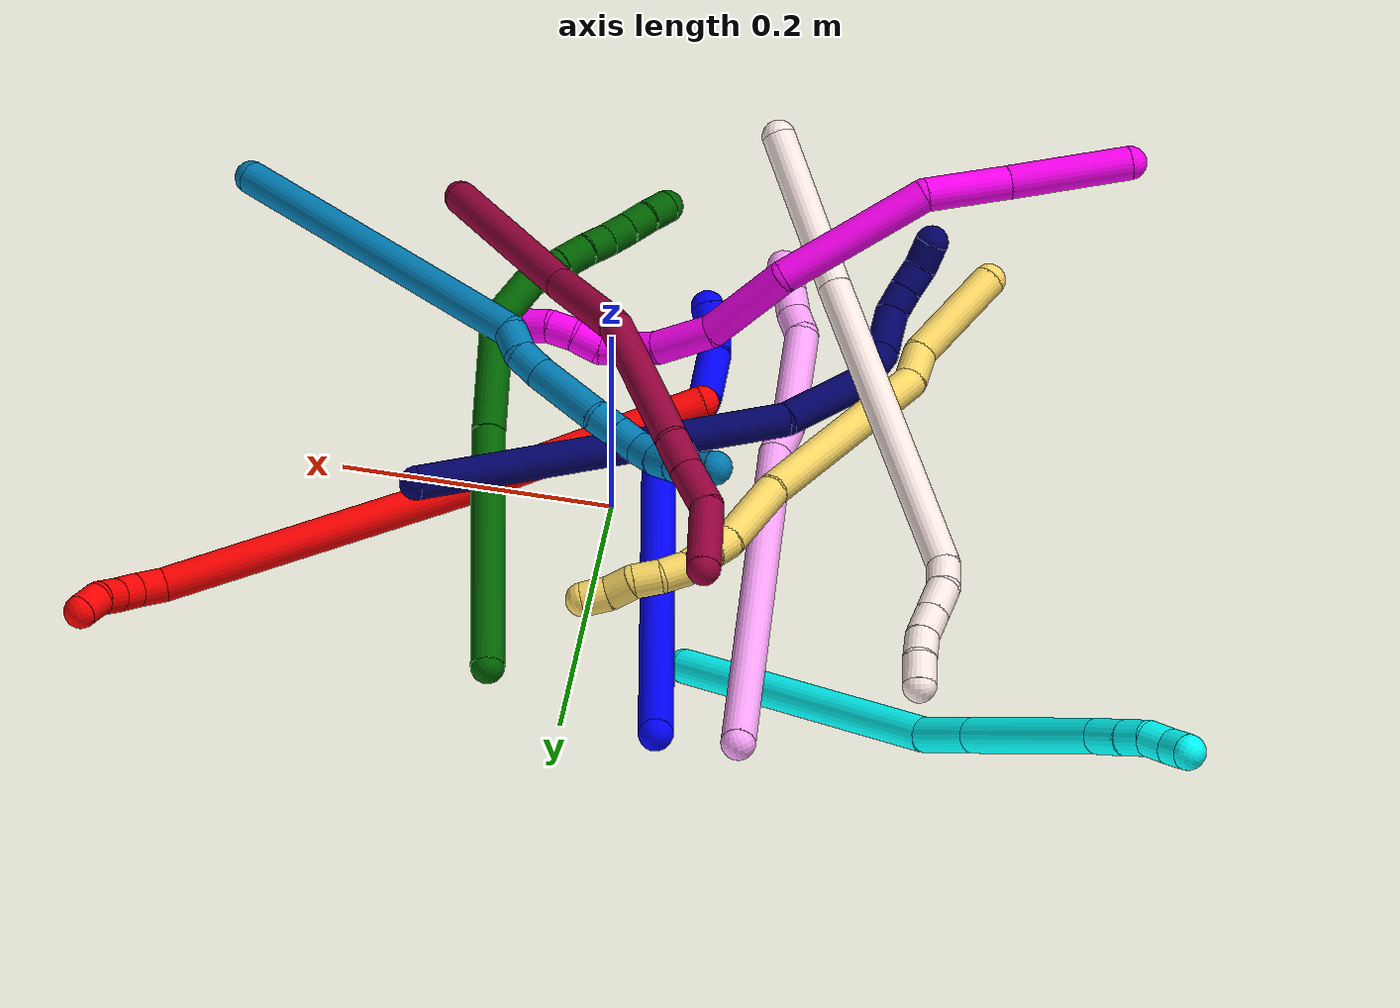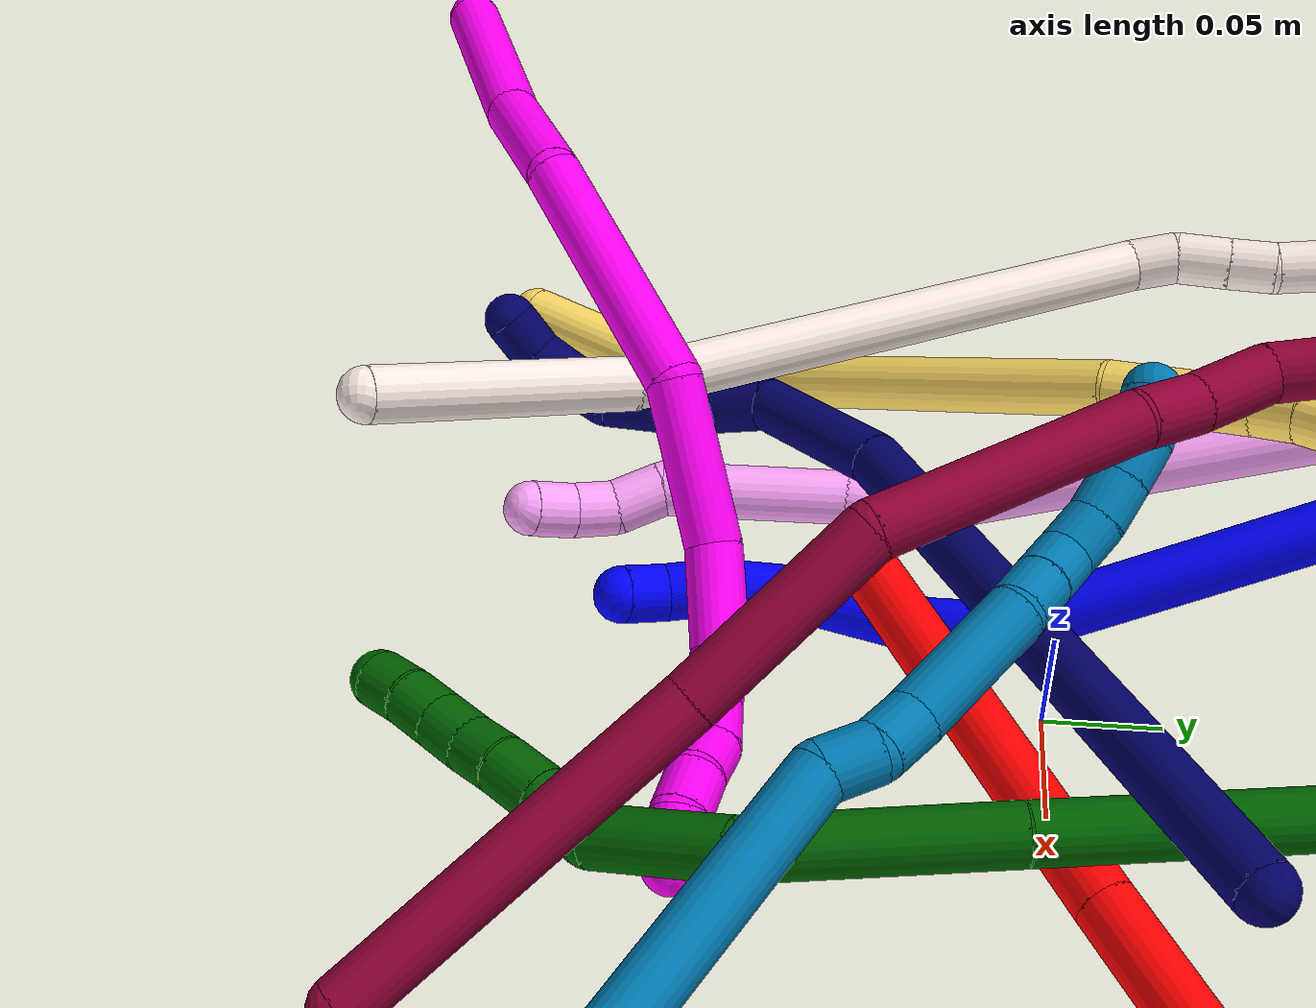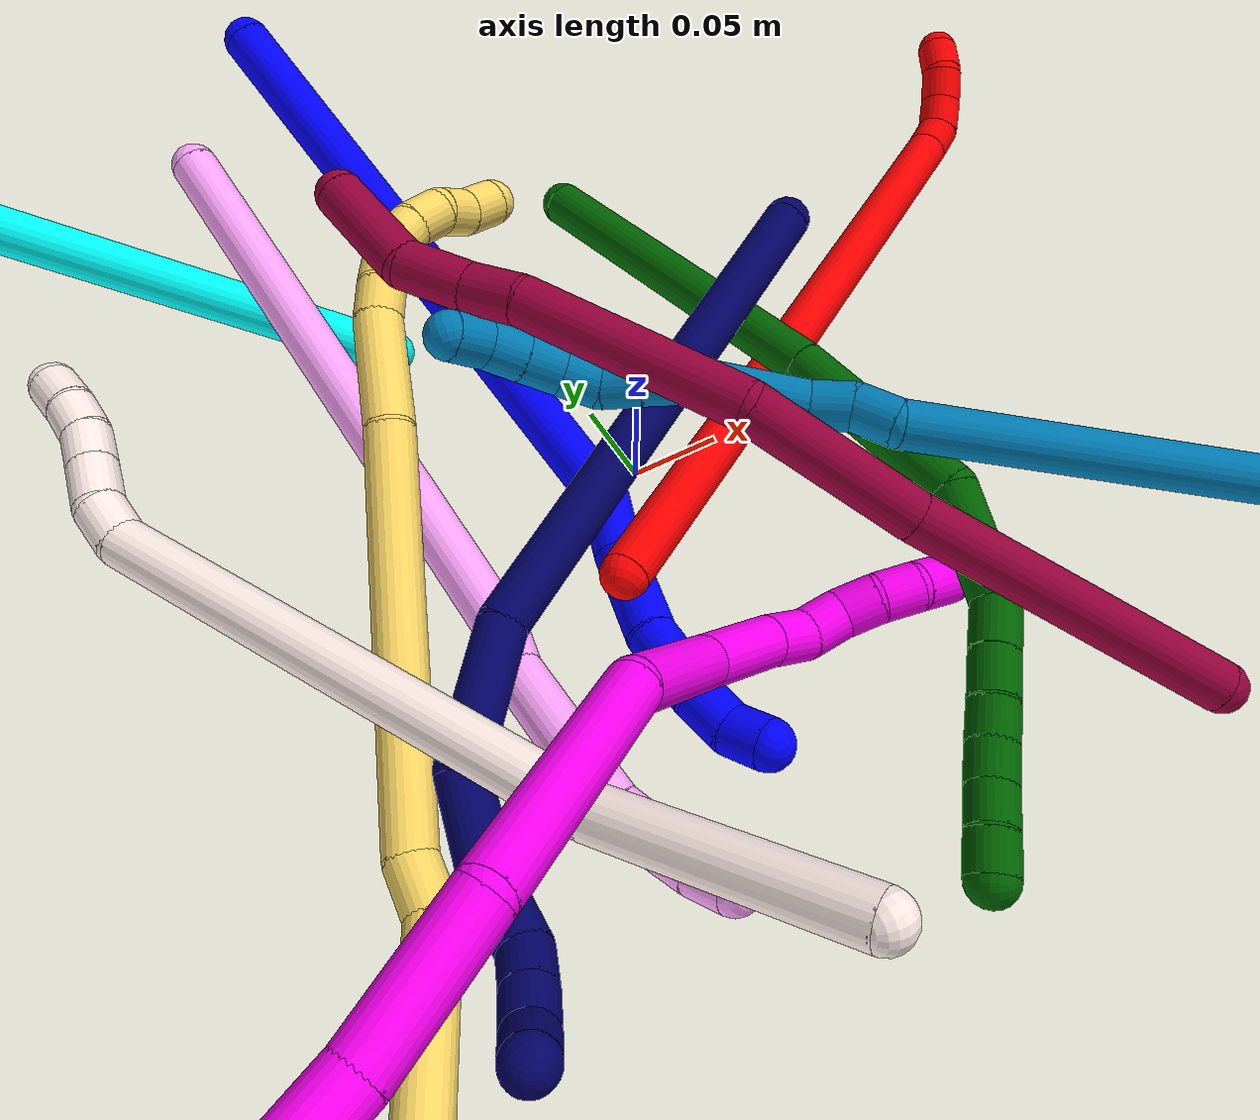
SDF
<sdf version="1.7">
 <world name="default">
  <plugin name="TubeGeneratorPlugin" filename="libtube_generator_plugin.so"/>
  <model name="photoneo_s_sensor">
   <static>1</static>
   <pose>0 0 2 1.57079 1.57079 3.14159</pose>
   <link name="link">
    <inertial><mass>0.1</mass></inertial>
    <sensor name="sensor" type="depth">
     <update_rate>30</update_rate>
     <camera>
      <horizontal_fov>1.22</horizontal_fov>
      <image><width>1920</width><height>1200</height><format>B8G8R8</format></image>
      <clip><near>0.1</near><far>4</far></clip>
      <depth_camera><output>points</output></depth_camera>
     </camera>
     <plugin name="camera_plugin" filename="libgazebo_ros_depth_camera.so">
      <baseline>0.2</baseline>
      <alwaysOn>1</alwaysOn>
      <updateRate>0.0</updateRate>
      <cameraName>camera_ir</cameraName>
      <imageTopicName>/camera/color/image_raw</imageTopicName>
      <cameraInfoTopicName>/camera/color/camera_info</cameraInfoTopicName>
      <depthImageTopicName>/camera/depth/image_raw</depthImageTopicName>
      <depthImageCameraInfoTopicName>/camera/depth/camera_info</depthImageCameraInfoTopicName>
      <pointCloudTopicName>/camera/depth/points</pointCloudTopicName>
      <frameName>fr_optical</frameName>
      <pointCloudCutoff>0.1</pointCloudCutoff>
      <pointCloudCutoffMax>2.0</pointCloudCutoffMax>
      <distortionK1>0</distortionK1>
      <distortionK2>0</distortionK2>
      <distortionK3>0</distortionK3>
      <distortionT1>0</distortionT1>
      <distortionT2>0</distortionT2>
      <CxPrime>0</CxPrime>
      <Cx>0</Cx>
      <Cy>0</Cy>
      <focalLength>0</focalLength>
      <hackBaseline>0</hackBaseline>
     </plugin>
    </sensor>
   </link>
  </model>
  <gravity>0 0 -9.8</gravity>
  <magnetic_field>6e-06 2.3e-05 -4.2e-05</magnetic_field>
  <atmosphere type="adiabatic"/>
  <physics name="default_physics" default="0" type="ode">
   <max_step_size>0.003</max_step_size>
   <real_time_factor>1</real_time_factor>
   <real_time_update_rate>1000</real_time_update_rate>
   <max_contacts>10000</max_contacts>
   <ode>
    <solver>
     <type>quick</type>
     <iters>100</iters>
     <sor>1.3</sor>
     <use_dynamic_moi_rescaling>0</use_dynamic_moi_rescaling>
    </solver>
    <constraints>
     <contact_max_correcting_vel>0</contact_max_correcting_vel>
     <contact_surface_layer>0.001</contact_surface_layer>
     <cfm>0</cfm>
     <erp>0.2</erp>
    </constraints>
   </ode>
  </physics>
  <scene><ambient>0.4 0.4 0.4 1</ambient><background>0.7 0.7 0.7 1</background><shadows>0</shadows></scene>
  <audio><device>default</device></audio>
  <spherical_coordinates>
   <surface_model>EARTH_WGS84</surface_model>
   <latitude_deg>0</latitude_deg>
   <longitude_deg>0</longitude_deg>
   <elevation>0</elevation>
   <heading_deg>0</heading_deg>
  </spherical_coordinates>
  <model name="bin">
   <static>1</static>
   <link name="bottom">
    <collision name="collision-bottom">
     <pose>0 0 -0.01 0 -0 0</pose>
     <geometry><box><size>0.8 0.6 0.02</size></box></geometry>
     <surface>
      <friction><ode><mu>100</mu><mu2>100</mu2></ode></friction>
      <contact><collide_bitmask>65535</collide_bitmask></contact>
     </surface>
    </collision>
   </link>
   <link name="west_wall">
    <collision name="collision-west_wall">
     <pose>-0.41 0 0.1 0 -0 0</pose>
     <geometry><box><size>0.02 0.6 0.2</size></box></geometry>
     <surface>
      <friction><ode><mu>100</mu><mu2>100</mu2></ode></friction>
      <contact><collide_bitmask>65535</collide_bitmask></contact>
     </surface>
    </collision>
   </link>
   <link name="east_wall">
    <collision name="collision-east_wall">
     <pose>0.41 0 0.1 0 -0 0</pose>
     <geometry><box><size>0.02 0.6 0.2</size></box></geometry>
     <surface>
      <friction><ode><mu>100</mu><mu2>100</mu2></ode></friction>
      <contact><collide_bitmask>65535</collide_bitmask></contact>
     </surface>
    </collision>
   </link>
   <link name="south_wall">
    <collision name="collision-south_wall">
     <pose>0 -0.31 0.1 0 -0 0</pose>
     <geometry><box><size>0.8 0.02 0.2</size></box></geometry>
     <surface>
      <friction><ode><mu>100</mu><mu2>100</mu2></ode></friction>
      <contact><collide_bitmask>65535</collide_bitmask></contact>
     </surface>
    </collision>
   </link>
   <link name="north_wall">
    <collision name="collision-north_wall">
     <pose>0 0.31 0.1 0 -0 0</pose>
     <geometry><box><size>0.8 0.02 0.2</size></box></geometry>
     <surface>
      <friction><ode><mu>100</mu><mu2>100</mu2></ode></friction>
      <contact><collide_bitmask>65535</collide_bitmask></contact>
     </surface>
    </collision>
   </link>
  </model>
  <model name="1">
   <static>0</static>
   <link name="1">
    <collision name="collision-cylinder-e_1_1_4">
     <pose>0.025386 -0.163034 0.0253 1.41684 0.152669 0.130872</pose>
     <geometry><cylinder><radius>0.0125</radius><length>0.333854</length></cylinder></geometry>
     <surface>
      <friction><ode><mu>1.16</mu><mu2>1.16</mu2><slip1>0</slip1><slip2>0</slip2></ode></friction>
      <contact><ode><kp>1e+06</kp><kd>1</kd><max_vel>0</max_vel><min_depth>0.001</min_depth></ode></contact>
     </surface>
    </collision>
    <visual name="visual-cylinder-e_1_1_4">
     <pose>0.025386 -0.163034 0.0253 1.41684 0.152669 0.130872</pose>
     <geometry><cylinder><radius>0.0125</radius><length>0.333854</length></cylinder></geometry>
     <material><ambient>0 0 1 1</ambient></material>
    </visual>
    <collision name="collision-cylinder-e_2_4_5">
     <pose>0.059387 -0.338659 0.052975 1.38444 0.591963 0.495259</pose>
     <geometry><cylinder><radius>0.0125</radius><length>0.030882</length></cylinder></geometry>
     <surface>
      <friction><ode><mu>1.16</mu><mu2>1.16</mu2><slip1>0</slip1><slip2>0</slip2></ode></friction>
      <contact><ode><kp>1e+06</kp><kd>1</kd><max_vel>0</max_vel><min_depth>0.001</min_depth></ode></contact>
     </surface>
    </collision>
    <visual name="visual-cylinder-e_2_4_5">
     <pose>0.059387 -0.338659 0.052975 1.38444 0.591963 0.495259</pose>
     <geometry><cylinder><radius>0.0125</radius><length>0.030882</length></cylinder></geometry>
     <material><ambient>0 0 1 1</ambient></material>
    </visual>
    <collision name="collision-cylinder-e_3_5_6">
     <pose>0.082614 -0.372696 0.050479 1.79409 0.586405 0.723054</pose>
     <geometry><cylinder><radius>0.0125</radius><length>0.052804</length></cylinder></geometry>
     <surface>
      <friction><ode><mu>1.16</mu><mu2>1.16</mu2><slip1>0</slip1><slip2>0</slip2></ode></friction>
      <contact><ode><kp>1e+06</kp><kd>1</kd><max_vel>0</max_vel><min_depth>0.001</min_depth></ode></contact>
     </surface>
    </collision>
    <visual name="visual-cylinder-e_3_5_6">
     <pose>0.082614 -0.372696 0.050479 1.79409 0.586405 0.723054</pose>
     <geometry><cylinder><radius>0.0125</radius><length>0.052804</length></cylinder></geometry>
     <material><ambient>0 0 1 1</ambient></material>
    </visual>
    <collision name="collision-cylinder-e_4_6_7">
     <pose>0.104323 -0.412543 0.041145 1.80881 0.358726 0.453199</pose>
     <geometry><cylinder><radius>0.0125</radius><length>0.040444</length></cylinder></geometry>
     <surface>
      <friction><ode><mu>1.16</mu><mu2>1.16</mu2><slip1>0</slip1><slip2>0</slip2></ode></friction>
      <contact><ode><kp>1e+06</kp><kd>1</kd><max_vel>0</max_vel><min_depth>0.001</min_depth></ode></contact>
     </surface>
    </collision>
    <visual name="visual-cylinder-e_4_6_7">
     <pose>0.104323 -0.412543 0.041145 1.80881 0.358726 0.453199</pose>
     <geometry><cylinder><radius>0.0125</radius><length>0.040444</length></cylinder></geometry>
     <material><ambient>0 0 1 1</ambient></material>
    </visual>
    <collision name="collision-cylinder-e_5_7_8">
     <pose>0.113199 -0.441605 0.035002 1.72699 0.163077 0.190612</pose>
     <geometry><cylinder><radius>0.0125</radius><length>0.021876</length></cylinder></geometry>
     <surface>
      <friction><ode><mu>1.16</mu><mu2>1.16</mu2><slip1>0</slip1><slip2>0</slip2></ode></friction>
      <contact><ode><kp>1e+06</kp><kd>1</kd><max_vel>0</max_vel><min_depth>0.001</min_depth></ode></contact>
     </surface>
    </collision>
    <visual name="visual-cylinder-e_5_7_8">
     <pose>0.113199 -0.441605 0.035002 1.72699 0.163077 0.190612</pose>
     <geometry><cylinder><radius>0.0125</radius><length>0.021876</length></cylinder></geometry>
     <material><ambient>0 0 1 1</ambient></material>
    </visual>
    <collision name="collision-cylinder-e_6_8_2">
     <pose>0.114466 -0.461071 0.028461 2.07541 -0.050559 -0.085649</pose>
     <geometry><cylinder><radius>0.0125</radius><length>0.02014</length></cylinder></geometry>
     <surface>
      <friction><ode><mu>1.16</mu><mu2>1.16</mu2><slip1>0</slip1><slip2>0</slip2></ode></friction>
      <contact><ode><kp>1e+06</kp><kd>1</kd><max_vel>0</max_vel><min_depth>0.001</min_depth></ode></contact>
     </surface>
    </collision>
    <visual name="visual-cylinder-e_6_8_2">
     <pose>0.114466 -0.461071 0.028461 2.07541 -0.050559 -0.085649</pose>
     <geometry><cylinder><radius>0.0125</radius><length>0.02014</length></cylinder></geometry>
     <material><ambient>0 0 1 1</ambient></material>
    </visual>
    <collision name="collision-sphere-2">
     <pose>0.113957 -0.469874 0.023598 0 -0 0</pose>
     <geometry><sphere><radius>0.0125</radius></sphere></geometry>
     <surface>
      <friction><ode><mu>1.16</mu><mu2>1.16</mu2><slip1>0</slip1><slip2>0</slip2></ode></friction>
      <contact><ode><kp>1e+06</kp><kd>1</kd><max_vel>0</max_vel><min_depth>0.001</min_depth></ode></contact>
     </surface>
    </collision>
    <visual name="visual-sphere-2">
     <pose>0.113957 -0.469874 0.023598 0 -0 0</pose>
     <geometry><sphere><radius>0.0125</radius></sphere></geometry>
     <material><ambient>0 0 1 1</ambient></material>
    </visual>
    <collision name="collision-sphere-4">
     <pose>0.050771 -0.326067 0.050601 0 -0 0</pose>
     <geometry><sphere><radius>0.0125</radius></sphere></geometry>
     <surface>
      <friction><ode><mu>1.16</mu><mu2>1.16</mu2><slip1>0</slip1><slip2>0</slip2></ode></friction>
      <contact><ode><kp>1e+06</kp><kd>1</kd><max_vel>0</max_vel><min_depth>0.001</min_depth></ode></contact>
     </surface>
    </collision>
    <visual name="visual-sphere-4">
     <pose>0.050771 -0.326067 0.050601 0 -0 0</pose>
     <geometry><sphere><radius>0.0125</radius></sphere></geometry>
     <material><ambient>0 0 1 1</ambient></material>
    </visual>
    <collision name="collision-sphere-1">
     <geometry><sphere><radius>0.0125</radius></sphere></geometry>
     <surface>
      <friction><ode><mu>1.16</mu><mu2>1.16</mu2><slip1>0</slip1><slip2>0</slip2></ode></friction>
      <contact><ode><kp>1e+06</kp><kd>1</kd><max_vel>0</max_vel><min_depth>0.001</min_depth></ode></contact>
     </surface>
    </collision>
    <visual name="visual-sphere-1">
     <geometry><sphere><radius>0.0125</radius></sphere></geometry>
     <material><ambient>0 0 1 1</ambient></material>
    </visual>
    <collision name="collision-sphere-8">
     <pose>0.114975 -0.452267 0.033323 0 -0 0</pose>
     <geometry><sphere><radius>0.0125</radius></sphere></geometry>
     <surface>
      <friction><ode><mu>1.16</mu><mu2>1.16</mu2><slip1>0</slip1><slip2>0</slip2></ode></friction>
      <contact><ode><kp>1e+06</kp><kd>1</kd><max_vel>0</max_vel><min_depth>0.001</min_depth></ode></contact>
     </surface>
    </collision>
    <visual name="visual-sphere-8">
     <pose>0.114975 -0.452267 0.033323 0 -0 0</pose>
     <geometry><sphere><radius>0.0125</radius></sphere></geometry>
     <material><ambient>0 0 1 1</ambient></material>
    </visual>
    <collision name="collision-sphere-5">
     <pose>0.068003 -0.351251 0.055349 0 -0 0</pose>
     <geometry><sphere><radius>0.0125</radius></sphere></geometry>
     <surface>
      <friction><ode><mu>1.16</mu><mu2>1.16</mu2><slip1>0</slip1><slip2>0</slip2></ode></friction>
      <contact><ode><kp>1e+06</kp><kd>1</kd><max_vel>0</max_vel><min_depth>0.001</min_depth></ode></contact>
     </surface>
    </collision>
    <visual name="visual-sphere-5">
     <pose>0.068003 -0.351251 0.055349 0 -0 0</pose>
     <geometry><sphere><radius>0.0125</radius></sphere></geometry>
     <material><ambient>0 0 1 1</ambient></material>
    </visual>
    <collision name="collision-sphere-6">
     <pose>0.097224 -0.394142 0.045609 0 -0 0</pose>
     <geometry><sphere><radius>0.0125</radius></sphere></geometry>
     <surface>
      <friction><ode><mu>1.16</mu><mu2>1.16</mu2><slip1>0</slip1><slip2>0</slip2></ode></friction>
      <contact><ode><kp>1e+06</kp><kd>1</kd><max_vel>0</max_vel><min_depth>0.001</min_depth></ode></contact>
     </surface>
    </collision>
    <visual name="visual-sphere-6">
     <pose>0.097224 -0.394142 0.045609 0 -0 0</pose>
     <geometry><sphere><radius>0.0125</radius></sphere></geometry>
     <material><ambient>0 0 1 1</ambient></material>
    </visual>
    <collision name="collision-sphere-7">
     <pose>0.111423 -0.430944 0.036681 0 -0 0</pose>
     <geometry><sphere><radius>0.0125</radius></sphere></geometry>
     <surface>
      <friction><ode><mu>1.16</mu><mu2>1.16</mu2><slip1>0</slip1><slip2>0</slip2></ode></friction>
      <contact><ode><kp>1e+06</kp><kd>1</kd><max_vel>0</max_vel><min_depth>0.001</min_depth></ode></contact>
     </surface>
    </collision>
    <visual name="visual-sphere-7">
     <pose>0.111423 -0.430944 0.036681 0 -0 0</pose>
     <geometry><sphere><radius>0.0125</radius></sphere></geometry>
     <material><ambient>0 0 1 1</ambient></material>
    </visual>
    <inertial>
     <pose>0.047345 -0.240399 0.031502 0 -0 0</pose>
     <mass>0.5</mass>
     <inertia>
      <ixx>0.003495</ixx>
      <ixy>0</ixy>
      <ixz>0</ixz>
      <iyy>0.000915</iyy>
      <iyz>0</iyz>
      <izz>0.002581</izz>
     </inertia>
    </inertial>
   </link>
   <pose>-0.085438 0.288505 0.13332 2.93434 -0.064028 -2.78097</pose>
  </model>
  <model name="2">
   <static>0</static>
   <link name="2">
    <collision name="collision-cylinder-e_1_1_4">
     <pose>0.022684 0.012614 0.087803 -0.14269 0.250363 -0.017986</pose>
     <geometry><cylinder><radius>0.0125</radius><length>0.183118</length></cylinder></geometry>
     <surface>
      <friction><ode><mu>1.16</mu><mu2>1.16</mu2><slip1>0</slip1><slip2>0</slip2></ode></friction>
      <contact><ode><kp>1e+06</kp><kd>1</kd><max_vel>0</max_vel><min_depth>0.001</min_depth></ode></contact>
     </surface>
    </collision>
    <visual name="visual-cylinder-e_1_1_4">
     <pose>0.022684 0.012614 0.087803 -0.14269 0.250363 -0.017986</pose>
     <geometry><cylinder><radius>0.0125</radius><length>0.183118</length></cylinder></geometry>
     <material><ambient>1 0 0 1</ambient></material>
    </visual>
    <collision name="collision-cylinder-e_2_4_5">
     <pose>0.073002 0.035198 0.289616 -0.087218 0.236925 -0.010387</pose>
     <geometry><cylinder><radius>0.0125</radius><length>0.235468</length></cylinder></geometry>
     <surface>
      <friction><ode><mu>1.16</mu><mu2>1.16</mu2><slip1>0</slip1><slip2>0</slip2></ode></friction>
      <contact><ode><kp>1e+06</kp><kd>1</kd><max_vel>0</max_vel><min_depth>0.001</min_depth></ode></contact>
     </surface>
    </collision>
    <visual name="visual-cylinder-e_2_4_5">
     <pose>0.073002 0.035198 0.289616 -0.087218 0.236925 -0.010387</pose>
     <geometry><cylinder><radius>0.0125</radius><length>0.235468</length></cylinder></geometry>
     <material><ambient>1 0 0 1</ambient></material>
    </visual>
    <collision name="collision-cylinder-e_3_5_6">
     <pose>0.102274 0.044412 0.413629 0.075314 0.161797 0.006109</pose>
     <geometry><cylinder><radius>0.0125</radius><length>0.020329</length></cylinder></geometry>
     <surface>
      <friction><ode><mu>1.16</mu><mu2>1.16</mu2><slip1>0</slip1><slip2>0</slip2></ode></friction>
      <contact><ode><kp>1e+06</kp><kd>1</kd><max_vel>0</max_vel><min_depth>0.001</min_depth></ode></contact>
     </surface>
    </collision>
    <visual name="visual-cylinder-e_3_5_6">
     <pose>0.102274 0.044412 0.413629 0.075314 0.161797 0.006109</pose>
     <geometry><cylinder><radius>0.0125</radius><length>0.020329</length></cylinder></geometry>
     <material><ambient>1 0 0 1</ambient></material>
    </visual>
    <collision name="collision-cylinder-e_4_6_7">
     <pose>0.101043 0.041232 0.433263 0.246651 -0.281152 -0.035078</pose>
     <geometry><cylinder><radius>0.0125</radius><length>0.020674</length></cylinder></geometry>
     <surface>
      <friction><ode><mu>1.16</mu><mu2>1.16</mu2><slip1>0</slip1><slip2>0</slip2></ode></friction>
      <contact><ode><kp>1e+06</kp><kd>1</kd><max_vel>0</max_vel><min_depth>0.001</min_depth></ode></contact>
     </surface>
    </collision>
    <visual name="visual-cylinder-e_4_6_7">
     <pose>0.101043 0.041232 0.433263 0.246651 -0.281152 -0.035078</pose>
     <geometry><cylinder><radius>0.0125</radius><length>0.020674</length></cylinder></geometry>
     <material><ambient>1 0 0 1</ambient></material>
    </visual>
    <collision name="collision-cylinder-e_5_7_8">
     <pose>0.09421 0.035436 0.451517 0.372734 -0.404564 -0.077302</pose>
     <geometry><cylinder><radius>0.0125</radius><length>0.020145</length></cylinder></geometry>
     <surface>
      <friction><ode><mu>1.16</mu><mu2>1.16</mu2><slip1>0</slip1><slip2>0</slip2></ode></friction>
      <contact><ode><kp>1e+06</kp><kd>1</kd><max_vel>0</max_vel><min_depth>0.001</min_depth></ode></contact>
     </surface>
    </collision>
    <visual name="visual-cylinder-e_5_7_8">
     <pose>0.09421 0.035436 0.451517 0.372734 -0.404564 -0.077302</pose>
     <geometry><cylinder><radius>0.0125</radius><length>0.020145</length></cylinder></geometry>
     <material><ambient>1 0 0 1</ambient></material>
    </visual>
    <collision name="collision-cylinder-e_6_8_2">
     <pose>0.086496 0.032608 0.469538 -0.057843 -0.379079 0.0111</pose>
     <geometry><cylinder><radius>0.0125</radius><length>0.020266</length></cylinder></geometry>
     <surface>
      <friction><ode><mu>1.16</mu><mu2>1.16</mu2><slip1>0</slip1><slip2>0</slip2></ode></friction>
      <contact><ode><kp>1e+06</kp><kd>1</kd><max_vel>0</max_vel><min_depth>0.001</min_depth></ode></contact>
     </surface>
    </collision>
    <visual name="visual-cylinder-e_6_8_2">
     <pose>0.086496 0.032608 0.469538 -0.057843 -0.379079 0.0111</pose>
     <geometry><cylinder><radius>0.0125</radius><length>0.020266</length></cylinder></geometry>
     <material><ambient>1 0 0 1</ambient></material>
    </visual>
    <collision name="collision-sphere-2">
     <pose>0.082746 0.033152 0.478937 0 -0 0</pose>
     <geometry><sphere><radius>0.0125</radius></sphere></geometry>
     <surface>
      <friction><ode><mu>1.16</mu><mu2>1.16</mu2><slip1>0</slip1><slip2>0</slip2></ode></friction>
      <contact><ode><kp>1e+06</kp><kd>1</kd><max_vel>0</max_vel><min_depth>0.001</min_depth></ode></contact>
     </surface>
    </collision>
    <visual name="visual-sphere-2">
     <pose>0.082746 0.033152 0.478937 0 -0 0</pose>
     <geometry><sphere><radius>0.0125</radius></sphere></geometry>
     <material><ambient>1 0 0 1</ambient></material>
    </visual>
    <collision name="collision-sphere-4">
     <pose>0.045368 0.025229 0.175606 0 -0 0</pose>
     <geometry><sphere><radius>0.0125</radius></sphere></geometry>
     <surface>
      <friction><ode><mu>1.16</mu><mu2>1.16</mu2><slip1>0</slip1><slip2>0</slip2></ode></friction>
      <contact><ode><kp>1e+06</kp><kd>1</kd><max_vel>0</max_vel><min_depth>0.001</min_depth></ode></contact>
     </surface>
    </collision>
    <visual name="visual-sphere-4">
     <pose>0.045368 0.025229 0.175606 0 -0 0</pose>
     <geometry><sphere><radius>0.0125</radius></sphere></geometry>
     <material><ambient>1 0 0 1</ambient></material>
    </visual>
    <collision name="collision-sphere-1">
     <geometry><sphere><radius>0.0125</radius></sphere></geometry>
     <surface>
      <friction><ode><mu>1.16</mu><mu2>1.16</mu2><slip1>0</slip1><slip2>0</slip2></ode></friction>
      <contact><ode><kp>1e+06</kp><kd>1</kd><max_vel>0</max_vel><min_depth>0.001</min_depth></ode></contact>
     </surface>
    </collision>
    <visual name="visual-sphere-1">
     <geometry><sphere><radius>0.0125</radius></sphere></geometry>
     <material><ambient>1 0 0 1</ambient></material>
    </visual>
    <collision name="collision-sphere-8">
     <pose>0.090246 0.032064 0.46014 0 -0 0</pose>
     <geometry><sphere><radius>0.0125</radius></sphere></geometry>
     <surface>
      <friction><ode><mu>1.16</mu><mu2>1.16</mu2><slip1>0</slip1><slip2>0</slip2></ode></friction>
      <contact><ode><kp>1e+06</kp><kd>1</kd><max_vel>0</max_vel><min_depth>0.001</min_depth></ode></contact>
     </surface>
    </collision>
    <visual name="visual-sphere-8">
     <pose>0.090246 0.032064 0.46014 0 -0 0</pose>
     <geometry><sphere><radius>0.0125</radius></sphere></geometry>
     <material><ambient>1 0 0 1</ambient></material>
    </visual>
    <collision name="collision-sphere-5">
     <pose>0.100636 0.045167 0.403626 0 -0 0</pose>
     <geometry><sphere><radius>0.0125</radius></sphere></geometry>
     <surface>
      <friction><ode><mu>1.16</mu><mu2>1.16</mu2><slip1>0</slip1><slip2>0</slip2></ode></friction>
      <contact><ode><kp>1e+06</kp><kd>1</kd><max_vel>0</max_vel><min_depth>0.001</min_depth></ode></contact>
     </surface>
    </collision>
    <visual name="visual-sphere-5">
     <pose>0.100636 0.045167 0.403626 0 -0 0</pose>
     <geometry><sphere><radius>0.0125</radius></sphere></geometry>
     <material><ambient>1 0 0 1</ambient></material>
    </visual>
    <collision name="collision-sphere-6">
     <pose>0.103911 0.043657 0.423632 0 -0 0</pose>
     <geometry><sphere><radius>0.0125</radius></sphere></geometry>
     <surface>
      <friction><ode><mu>1.16</mu><mu2>1.16</mu2><slip1>0</slip1><slip2>0</slip2></ode></friction>
      <contact><ode><kp>1e+06</kp><kd>1</kd><max_vel>0</max_vel><min_depth>0.001</min_depth></ode></contact>
     </surface>
    </collision>
    <visual name="visual-sphere-6">
     <pose>0.103911 0.043657 0.423632 0 -0 0</pose>
     <geometry><sphere><radius>0.0125</radius></sphere></geometry>
     <material><ambient>1 0 0 1</ambient></material>
    </visual>
    <collision name="collision-sphere-7">
     <pose>0.098175 0.038808 0.442894 0 -0 0</pose>
     <geometry><sphere><radius>0.0125</radius></sphere></geometry>
     <surface>
      <friction><ode><mu>1.16</mu><mu2>1.16</mu2><slip1>0</slip1><slip2>0</slip2></ode></friction>
      <contact><ode><kp>1e+06</kp><kd>1</kd><max_vel>0</max_vel><min_depth>0.001</min_depth></ode></contact>
     </surface>
    </collision>
    <visual name="visual-sphere-7">
     <pose>0.098175 0.038808 0.442894 0 -0 0</pose>
     <geometry><sphere><radius>0.0125</radius></sphere></geometry>
     <material><ambient>1 0 0 1</ambient></material>
    </visual>
    <inertial>
     <pose>0.058325 0.027456 0.240502 0 -0 0</pose>
     <mass>0.5</mass>
     <inertia>
      <ixx>0.001561</ixx>
      <ixy>0</ixy>
      <ixz>0</ixz>
      <iyy>0.001595</iyy>
      <iyz>0</iyz>
      <izz>-0.000511</izz>
     </inertia>
    </inertial>
   </link>
   <pose>-0.052482 -0.078413 0.037602 -1.40792 0.451378 -0.783906</pose>
  </model>
  <model name="3">
   <static>0</static>
   <link name="3">
    <collision name="collision-cylinder-e_1_1_4">
     <pose>-0.012061 0.01303 0.11854 -0.10948 -0.100792 0.005528</pose>
     <geometry><cylinder><radius>0.0125</radius><length>0.239725</length></cylinder></geometry>
     <surface>
      <friction><ode><mu>1.16</mu><mu2>1.16</mu2><slip1>0</slip1><slip2>0</slip2></ode></friction>
      <contact><ode><kp>1e+06</kp><kd>1</kd><max_vel>0</max_vel><min_depth>0.001</min_depth></ode></contact>
     </surface>
    </collision>
    <visual name="visual-cylinder-e_1_1_4">
     <pose>-0.012061 0.01303 0.11854 -0.10948 -0.100792 0.005528</pose>
     <geometry><cylinder><radius>0.0125</radius><length>0.239725</length></cylinder></geometry>
     <material><ambient>0.003922 1 0.996078 1</ambient></material>
    </visual>
    <collision name="collision-cylinder-e_2_4_5">
     <pose>-0.029994 0.025009 0.260518 0.044815 -0.245278 -0.005525</pose>
     <geometry><cylinder><radius>0.0125</radius><length>0.048371</length></cylinder></geometry>
     <surface>
      <friction><ode><mu>1.16</mu><mu2>1.16</mu2><slip1>0</slip1><slip2>0</slip2></ode></friction>
      <contact><ode><kp>1e+06</kp><kd>1</kd><max_vel>0</max_vel><min_depth>0.001</min_depth></ode></contact>
     </surface>
    </collision>
    <visual name="visual-cylinder-e_2_4_5">
     <pose>-0.029994 0.025009 0.260518 0.044815 -0.245278 -0.005525</pose>
     <geometry><cylinder><radius>0.0125</radius><length>0.048371</length></cylinder></geometry>
     <material><ambient>0.003922 1 0.996078 1</ambient></material>
    </visual>
    <collision name="collision-cylinder-e_3_5_6">
     <pose>-0.05082 0.021199 0.343002 0.046687 -0.247777 -0.005815</pose>
     <geometry><cylinder><radius>0.0125</radius><length>0.121943</length></cylinder></geometry>
     <surface>
      <friction><ode><mu>1.16</mu><mu2>1.16</mu2><slip1>0</slip1><slip2>0</slip2></ode></friction>
      <contact><ode><kp>1e+06</kp><kd>1</kd><max_vel>0</max_vel><min_depth>0.001</min_depth></ode></contact>
     </surface>
    </collision>
    <visual name="visual-cylinder-e_3_5_6">
     <pose>-0.05082 0.021199 0.343002 0.046687 -0.247777 -0.005815</pose>
     <geometry><cylinder><radius>0.0125</radius><length>0.121943</length></cylinder></geometry>
     <material><ambient>0.003922 1 0.996078 1</ambient></material>
    </visual>
    <collision name="collision-cylinder-e_4_6_7">
     <pose>-0.068657 0.01776 0.415965 0.04884 -0.20404 -0.005001</pose>
     <geometry><cylinder><radius>0.0125</radius><length>0.02846</length></cylinder></geometry>
     <surface>
      <friction><ode><mu>1.16</mu><mu2>1.16</mu2><slip1>0</slip1><slip2>0</slip2></ode></friction>
      <contact><ode><kp>1e+06</kp><kd>1</kd><max_vel>0</max_vel><min_depth>0.001</min_depth></ode></contact>
     </surface>
    </collision>
    <visual name="visual-cylinder-e_4_6_7">
     <pose>-0.068657 0.01776 0.415965 0.04884 -0.20404 -0.005001</pose>
     <geometry><cylinder><radius>0.0125</radius><length>0.02846</length></cylinder></geometry>
     <material><ambient>0.003922 1 0.996078 1</ambient></material>
    </visual>
    <collision name="collision-cylinder-e_5_7_8">
     <pose>-0.074314 0.017017 0.440088 0.006168 -0.265338 -0.000823</pose>
     <geometry><cylinder><radius>0.0125</radius><length>0.021152</length></cylinder></geometry>
     <surface>
      <friction><ode><mu>1.16</mu><mu2>1.16</mu2><slip1>0</slip1><slip2>0</slip2></ode></friction>
      <contact><ode><kp>1e+06</kp><kd>1</kd><max_vel>0</max_vel><min_depth>0.001</min_depth></ode></contact>
     </surface>
    </collision>
    <visual name="visual-cylinder-e_5_7_8">
     <pose>-0.074314 0.017017 0.440088 0.006168 -0.265338 -0.000823</pose>
     <geometry><cylinder><radius>0.0125</radius><length>0.021152</length></cylinder></geometry>
     <material><ambient>0.003922 1 0.996078 1</ambient></material>
    </visual>
    <collision name="collision-cylinder-e_6_8_9">
     <pose>-0.077675 0.019047 0.46012 -0.209875 -0.058485 0.006162</pose>
     <geometry><cylinder><radius>0.0125</radius><length>0.020128</length></cylinder></geometry>
     <surface>
      <friction><ode><mu>1.16</mu><mu2>1.16</mu2><slip1>0</slip1><slip2>0</slip2></ode></friction>
      <contact><ode><kp>1e+06</kp><kd>1</kd><max_vel>0</max_vel><min_depth>0.001</min_depth></ode></contact>
     </surface>
    </collision>
    <visual name="visual-cylinder-e_6_8_9">
     <pose>-0.077675 0.019047 0.46012 -0.209875 -0.058485 0.006162</pose>
     <geometry><cylinder><radius>0.0125</radius><length>0.020128</length></cylinder></geometry>
     <material><ambient>0.003922 1 0.996078 1</ambient></material>
    </visual>
    <collision name="collision-cylinder-e_7_9_2">
     <pose>-0.078443 0.020338 0.480024 0.079439 -0.017704 -0.000704</pose>
     <geometry><cylinder><radius>0.0125</radius><length>0.020222</length></cylinder></geometry>
     <surface>
      <friction><ode><mu>1.16</mu><mu2>1.16</mu2><slip1>0</slip1><slip2>0</slip2></ode></friction>
      <contact><ode><kp>1e+06</kp><kd>1</kd><max_vel>0</max_vel><min_depth>0.001</min_depth></ode></contact>
     </surface>
    </collision>
    <visual name="visual-cylinder-e_7_9_2">
     <pose>-0.078443 0.020338 0.480024 0.079439 -0.017704 -0.000704</pose>
     <geometry><cylinder><radius>0.0125</radius><length>0.020222</length></cylinder></geometry>
     <material><ambient>0.003922 1 0.996078 1</ambient></material>
    </visual>
    <collision name="collision-sphere-2">
     <pose>-0.078622 0.019535 0.490101 0 -0 0</pose>
     <geometry><sphere><radius>0.0125</radius></sphere></geometry>
     <surface>
      <friction><ode><mu>1.16</mu><mu2>1.16</mu2><slip1>0</slip1><slip2>0</slip2></ode></friction>
      <contact><ode><kp>1e+06</kp><kd>1</kd><max_vel>0</max_vel><min_depth>0.001</min_depth></ode></contact>
     </surface>
    </collision>
    <visual name="visual-sphere-2">
     <pose>-0.078622 0.019535 0.490101 0 -0 0</pose>
     <geometry><sphere><radius>0.0125</radius></sphere></geometry>
     <material><ambient>0.003922 1 0.996078 1</ambient></material>
    </visual>
    <collision name="collision-sphere-9">
     <pose>-0.078264 0.02114 0.469946 0 -0 0</pose>
     <geometry><sphere><radius>0.0125</radius></sphere></geometry>
     <surface>
      <friction><ode><mu>1.16</mu><mu2>1.16</mu2><slip1>0</slip1><slip2>0</slip2></ode></friction>
      <contact><ode><kp>1e+06</kp><kd>1</kd><max_vel>0</max_vel><min_depth>0.001</min_depth></ode></contact>
     </surface>
    </collision>
    <visual name="visual-sphere-9">
     <pose>-0.078264 0.02114 0.469946 0 -0 0</pose>
     <geometry><sphere><radius>0.0125</radius></sphere></geometry>
     <material><ambient>0.003922 1 0.996078 1</ambient></material>
    </visual>
    <collision name="collision-sphere-4">
     <pose>-0.024122 0.02606 0.23708 0 -0 0</pose>
     <geometry><sphere><radius>0.0125</radius></sphere></geometry>
     <surface>
      <friction><ode><mu>1.16</mu><mu2>1.16</mu2><slip1>0</slip1><slip2>0</slip2></ode></friction>
      <contact><ode><kp>1e+06</kp><kd>1</kd><max_vel>0</max_vel><min_depth>0.001</min_depth></ode></contact>
     </surface>
    </collision>
    <visual name="visual-sphere-4">
     <pose>-0.024122 0.02606 0.23708 0 -0 0</pose>
     <geometry><sphere><radius>0.0125</radius></sphere></geometry>
     <material><ambient>0.003922 1 0.996078 1</ambient></material>
    </visual>
    <collision name="collision-sphere-1">
     <geometry><sphere><radius>0.0125</radius></sphere></geometry>
     <surface>
      <friction><ode><mu>1.16</mu><mu2>1.16</mu2><slip1>0</slip1><slip2>0</slip2></ode></friction>
      <contact><ode><kp>1e+06</kp><kd>1</kd><max_vel>0</max_vel><min_depth>0.001</min_depth></ode></contact>
     </surface>
    </collision>
    <visual name="visual-sphere-1">
     <geometry><sphere><radius>0.0125</radius></sphere></geometry>
     <material><ambient>0.003922 1 0.996078 1</ambient></material>
    </visual>
    <collision name="collision-sphere-8">
     <pose>-0.077087 0.016954 0.450294 0 -0 0</pose>
     <geometry><sphere><radius>0.0125</radius></sphere></geometry>
     <surface>
      <friction><ode><mu>1.16</mu><mu2>1.16</mu2><slip1>0</slip1><slip2>0</slip2></ode></friction>
      <contact><ode><kp>1e+06</kp><kd>1</kd><max_vel>0</max_vel><min_depth>0.001</min_depth></ode></contact>
     </surface>
    </collision>
    <visual name="visual-sphere-8">
     <pose>-0.077087 0.016954 0.450294 0 -0 0</pose>
     <geometry><sphere><radius>0.0125</radius></sphere></geometry>
     <material><ambient>0.003922 1 0.996078 1</ambient></material>
    </visual>
    <collision name="collision-sphere-5">
     <pose>-0.035867 0.023958 0.283957 0 -0 0</pose>
     <geometry><sphere><radius>0.0125</radius></sphere></geometry>
     <surface>
      <friction><ode><mu>1.16</mu><mu2>1.16</mu2><slip1>0</slip1><slip2>0</slip2></ode></friction>
      <contact><ode><kp>1e+06</kp><kd>1</kd><max_vel>0</max_vel><min_depth>0.001</min_depth></ode></contact>
     </surface>
    </collision>
    <visual name="visual-sphere-5">
     <pose>-0.035867 0.023958 0.283957 0 -0 0</pose>
     <geometry><sphere><radius>0.0125</radius></sphere></geometry>
     <material><ambient>0.003922 1 0.996078 1</ambient></material>
    </visual>
    <collision name="collision-sphere-6">
     <pose>-0.065774 0.01844 0.402046 0 -0 0</pose>
     <geometry><sphere><radius>0.0125</radius></sphere></geometry>
     <surface>
      <friction><ode><mu>1.16</mu><mu2>1.16</mu2><slip1>0</slip1><slip2>0</slip2></ode></friction>
      <contact><ode><kp>1e+06</kp><kd>1</kd><max_vel>0</max_vel><min_depth>0.001</min_depth></ode></contact>
     </surface>
    </collision>
    <visual name="visual-sphere-6">
     <pose>-0.065774 0.01844 0.402046 0 -0 0</pose>
     <geometry><sphere><radius>0.0125</radius></sphere></geometry>
     <material><ambient>0.003922 1 0.996078 1</ambient></material>
    </visual>
    <collision name="collision-sphere-7">
     <pose>-0.07154 0.01708 0.429883 0 -0 0</pose>
     <geometry><sphere><radius>0.0125</radius></sphere></geometry>
     <surface>
      <friction><ode><mu>1.16</mu><mu2>1.16</mu2><slip1>0</slip1><slip2>0</slip2></ode></friction>
      <contact><ode><kp>1e+06</kp><kd>1</kd><max_vel>0</max_vel><min_depth>0.001</min_depth></ode></contact>
     </surface>
    </collision>
    <visual name="visual-sphere-7">
     <pose>-0.07154 0.01708 0.429883 0 -0 0</pose>
     <geometry><sphere><radius>0.0125</radius></sphere></geometry>
     <material><ambient>0.003922 1 0.996078 1</ambient></material>
    </visual>
    <inertial>
     <pose>-0.03443 0.017157 0.24592 0 -0 0</pose>
     <mass>0.5</mass>
     <inertia><ixx>0.00132</ixx><ixy>0</ixy><ixz>0</ixz><iyy>0.001332</iyy><iyz>0</iyz><izz>7.9e-05</izz></inertia>
    </inertial>
   </link>
   <pose>-0.079342 0.139931 0.011487 -1.0122 0.38268 1.14662</pose>
  </model>
  <model name="4">
   <static>0</static>
   <link name="4">
    <collision name="collision-cylinder-e_1_1_4">
     <pose>0.017909 -0.148544 0.064642 1.16034 0.110103 0.072204</pose>
     <geometry><cylinder><radius>0.0125</radius><length>0.325973</length></cylinder></geometry>
     <surface>
      <friction><ode><mu>1.16</mu><mu2>1.16</mu2><slip1>0</slip1><slip2>0</slip2></ode></friction>
      <contact><ode><kp>1e+06</kp><kd>1</kd><max_vel>0</max_vel><min_depth>0.001</min_depth></ode></contact>
     </surface>
    </collision>
    <visual name="visual-cylinder-e_1_1_4">
     <pose>0.017909 -0.148544 0.064642 1.16034 0.110103 0.072204</pose>
     <geometry><cylinder><radius>0.0125</radius><length>0.325973</length></cylinder></geometry>
     <material><ambient>1 0.65098 0.996078 1</ambient></material>
    </visual>
    <collision name="collision-cylinder-e_2_4_5">
     <pose>0.032358 -0.307854 0.135327 1.05925 -0.273269 -0.160632</pose>
     <geometry><cylinder><radius>0.0125</radius><length>0.025644</length></cylinder></geometry>
     <surface>
      <friction><ode><mu>1.16</mu><mu2>1.16</mu2><slip1>0</slip1><slip2>0</slip2></ode></friction>
      <contact><ode><kp>1e+06</kp><kd>1</kd><max_vel>0</max_vel><min_depth>0.001</min_depth></ode></contact>
     </surface>
    </collision>
    <visual name="visual-cylinder-e_2_4_5">
     <pose>0.032358 -0.307854 0.135327 1.05925 -0.273269 -0.160632</pose>
     <geometry><cylinder><radius>0.0125</radius><length>0.025644</length></cylinder></geometry>
     <material><ambient>1 0.65098 0.996078 1</ambient></material>
    </visual>
    <collision name="collision-cylinder-e_3_5_6">
     <pose>0.026417 -0.352515 0.166491 0.933008 -0.058729 -0.029581</pose>
     <geometry><cylinder><radius>0.0125</radius><length>0.084524</length></cylinder></geometry>
     <surface>
      <friction><ode><mu>1.16</mu><mu2>1.16</mu2><slip1>0</slip1><slip2>0</slip2></ode></friction>
      <contact><ode><kp>1e+06</kp><kd>1</kd><max_vel>0</max_vel><min_depth>0.001</min_depth></ode></contact>
     </surface>
    </collision>
    <visual name="visual-cylinder-e_3_5_6">
     <pose>0.026417 -0.352515 0.166491 0.933008 -0.058729 -0.029581</pose>
     <geometry><cylinder><radius>0.0125</radius><length>0.084524</length></cylinder></geometry>
     <material><ambient>1 0.65098 0.996078 1</ambient></material>
    </visual>
    <collision name="collision-cylinder-e_4_6_7">
     <pose>0.028411 -0.395431 0.197957 0.957718 0.385485 0.201955</pose>
     <geometry><cylinder><radius>0.0125</radius><length>0.023804</length></cylinder></geometry>
     <surface>
      <friction><ode><mu>1.16</mu><mu2>1.16</mu2><slip1>0</slip1><slip2>0</slip2></ode></friction>
      <contact><ode><kp>1e+06</kp><kd>1</kd><max_vel>0</max_vel><min_depth>0.001</min_depth></ode></contact>
     </surface>
    </collision>
    <visual name="visual-cylinder-e_4_6_7">
     <pose>0.028411 -0.395431 0.197957 0.957718 0.385485 0.201955</pose>
     <geometry><cylinder><radius>0.0125</radius><length>0.023804</length></cylinder></geometry>
     <material><ambient>1 0.65098 0.996078 1</ambient></material>
    </visual>
    <collision name="collision-cylinder-e_5_7_8">
     <pose>0.034183 -0.410806 0.211917 0.695494 0.130005 0.047182</pose>
     <geometry><cylinder><radius>0.0125</radius><length>0.020003</length></cylinder></geometry>
     <surface>
      <friction><ode><mu>1.16</mu><mu2>1.16</mu2><slip1>0</slip1><slip2>0</slip2></ode></friction>
      <contact><ode><kp>1e+06</kp><kd>1</kd><max_vel>0</max_vel><min_depth>0.001</min_depth></ode></contact>
     </surface>
    </collision>
    <visual name="visual-cylinder-e_5_7_8">
     <pose>0.034183 -0.410806 0.211917 0.695494 0.130005 0.047182</pose>
     <geometry><cylinder><radius>0.0125</radius><length>0.020003</length></cylinder></geometry>
     <material><ambient>1 0.65098 0.996078 1</ambient></material>
    </visual>
    <collision name="collision-cylinder-e_6_8_2">
     <pose>0.036217 -0.421692 0.228443 0.47045 0.07361 0.017649</pose>
     <geometry><cylinder><radius>0.0125</radius><length>0.020051</length></cylinder></geometry>
     <surface>
      <friction><ode><mu>1.16</mu><mu2>1.16</mu2><slip1>0</slip1><slip2>0</slip2></ode></friction>
      <contact><ode><kp>1e+06</kp><kd>1</kd><max_vel>0</max_vel><min_depth>0.001</min_depth></ode></contact>
     </surface>
    </collision>
    <visual name="visual-cylinder-e_6_8_2">
     <pose>0.036217 -0.421692 0.228443 0.47045 0.07361 0.017649</pose>
     <geometry><cylinder><radius>0.0125</radius><length>0.020051</length></cylinder></geometry>
     <material><ambient>1 0.65098 0.996078 1</ambient></material>
    </visual>
    <collision name="collision-sphere-2">
     <pose>0.036955 -0.426224 0.237355 0 -0 0</pose>
     <geometry><sphere><radius>0.0125</radius></sphere></geometry>
     <surface>
      <friction><ode><mu>1.16</mu><mu2>1.16</mu2><slip1>0</slip1><slip2>0</slip2></ode></friction>
      <contact><ode><kp>1e+06</kp><kd>1</kd><max_vel>0</max_vel><min_depth>0.001</min_depth></ode></contact>
     </surface>
    </collision>
    <visual name="visual-sphere-2">
     <pose>0.036955 -0.426224 0.237355 0 -0 0</pose>
     <geometry><sphere><radius>0.0125</radius></sphere></geometry>
     <material><ambient>1 0.65098 0.996078 1</ambient></material>
    </visual>
    <collision name="collision-sphere-4">
     <pose>0.035818 -0.297088 0.129283 0 -0 0</pose>
     <geometry><sphere><radius>0.0125</radius></sphere></geometry>
     <surface>
      <friction><ode><mu>1.16</mu><mu2>1.16</mu2><slip1>0</slip1><slip2>0</slip2></ode></friction>
      <contact><ode><kp>1e+06</kp><kd>1</kd><max_vel>0</max_vel><min_depth>0.001</min_depth></ode></contact>
     </surface>
    </collision>
    <visual name="visual-sphere-4">
     <pose>0.035818 -0.297088 0.129283 0 -0 0</pose>
     <geometry><sphere><radius>0.0125</radius></sphere></geometry>
     <material><ambient>1 0.65098 0.996078 1</ambient></material>
    </visual>
    <collision name="collision-sphere-1">
     <geometry><sphere><radius>0.0125</radius></sphere></geometry>
     <surface>
      <friction><ode><mu>1.16</mu><mu2>1.16</mu2><slip1>0</slip1><slip2>0</slip2></ode></friction>
      <contact><ode><kp>1e+06</kp><kd>1</kd><max_vel>0</max_vel><min_depth>0.001</min_depth></ode></contact>
     </surface>
    </collision>
    <visual name="visual-sphere-1">
     <geometry><sphere><radius>0.0125</radius></sphere></geometry>
     <material><ambient>1 0.65098 0.996078 1</ambient></material>
    </visual>
    <collision name="collision-sphere-8">
     <pose>0.03548 -0.41716 0.219531 0 -0 0</pose>
     <geometry><sphere><radius>0.0125</radius></sphere></geometry>
     <surface>
      <friction><ode><mu>1.16</mu><mu2>1.16</mu2><slip1>0</slip1><slip2>0</slip2></ode></friction>
      <contact><ode><kp>1e+06</kp><kd>1</kd><max_vel>0</max_vel><min_depth>0.001</min_depth></ode></contact>
     </surface>
    </collision>
    <visual name="visual-sphere-8">
     <pose>0.03548 -0.41716 0.219531 0 -0 0</pose>
     <geometry><sphere><radius>0.0125</radius></sphere></geometry>
     <material><ambient>1 0.65098 0.996078 1</ambient></material>
    </visual>
    <collision name="collision-sphere-5">
     <pose>0.028897 -0.31862 0.141371 0 -0 0</pose>
     <geometry><sphere><radius>0.0125</radius></sphere></geometry>
     <surface>
      <friction><ode><mu>1.16</mu><mu2>1.16</mu2><slip1>0</slip1><slip2>0</slip2></ode></friction>
      <contact><ode><kp>1e+06</kp><kd>1</kd><max_vel>0</max_vel><min_depth>0.001</min_depth></ode></contact>
     </surface>
    </collision>
    <visual name="visual-sphere-5">
     <pose>0.028897 -0.31862 0.141371 0 -0 0</pose>
     <geometry><sphere><radius>0.0125</radius></sphere></geometry>
     <material><ambient>1 0.65098 0.996078 1</ambient></material>
    </visual>
    <collision name="collision-sphere-6">
     <pose>0.023936 -0.38641 0.191611 0 -0 0</pose>
     <geometry><sphere><radius>0.0125</radius></sphere></geometry>
     <surface>
      <friction><ode><mu>1.16</mu><mu2>1.16</mu2><slip1>0</slip1><slip2>0</slip2></ode></friction>
      <contact><ode><kp>1e+06</kp><kd>1</kd><max_vel>0</max_vel><min_depth>0.001</min_depth></ode></contact>
     </surface>
    </collision>
    <visual name="visual-sphere-6">
     <pose>0.023936 -0.38641 0.191611 0 -0 0</pose>
     <geometry><sphere><radius>0.0125</radius></sphere></geometry>
     <material><ambient>1 0.65098 0.996078 1</ambient></material>
    </visual>
    <collision name="collision-sphere-7">
     <pose>0.032887 -0.404451 0.204303 0 -0 0</pose>
     <geometry><sphere><radius>0.0125</radius></sphere></geometry>
     <surface>
      <friction><ode><mu>1.16</mu><mu2>1.16</mu2><slip1>0</slip1><slip2>0</slip2></ode></friction>
      <contact><ode><kp>1e+06</kp><kd>1</kd><max_vel>0</max_vel><min_depth>0.001</min_depth></ode></contact>
     </surface>
    </collision>
    <visual name="visual-sphere-7">
     <pose>0.032887 -0.404451 0.204303 0 -0 0</pose>
     <geometry><sphere><radius>0.0125</radius></sphere></geometry>
     <material><ambient>1 0.65098 0.996078 1</ambient></material>
    </visual>
    <inertial>
     <pose>0.021974 -0.224396 0.104292 0 -0 0</pose>
     <mass>0.5</mass>
     <inertia>
      <ixx>0.003144</ixx>
      <ixy>0</ixy>
      <ixz>0</ixz>
      <iyy>0.001385</iyy>
      <iyz>0</iyz>
      <izz>0.002393</izz>
     </inertia>
    </inertial>
   </link>
   <pose>-0.138283 0.254445 0.089044 0.623965 0.514666 0.095925</pose>
  </model>
  <model name="5">
   <static>0</static>
   <link name="5">
    <collision name="collision-cylinder-e_1_1_4">
     <pose>0.013044 0.035104 0.020319 -1.0461 0.31114 -0.18038</pose>
     <geometry><cylinder><radius>0.0125</radius><length>0.085211</length></cylinder></geometry>
     <surface>
      <friction><ode><mu>1.16</mu><mu2>1.16</mu2><slip1>0</slip1><slip2>0</slip2></ode></friction>
      <contact><ode><kp>1e+06</kp><kd>1</kd><max_vel>0</max_vel><min_depth>0.001</min_depth></ode></contact>
     </surface>
    </collision>
    <visual name="visual-cylinder-e_1_1_4">
     <pose>0.013044 0.035104 0.020319 -1.0461 0.31114 -0.18038</pose>
     <geometry><cylinder><radius>0.0125</radius><length>0.085211</length></cylinder></geometry>
     <material><ambient>1 0.858824 0.4 1</ambient></material>
    </visual>
    <collision name="collision-cylinder-e_2_4_5">
     <pose>0.034379 0.0813 0.043648 -1.30581 0.624935 -0.484433</pose>
     <geometry><cylinder><radius>0.0125</radius><length>0.028345</length></cylinder></geometry>
     <surface>
      <friction><ode><mu>1.16</mu><mu2>1.16</mu2><slip1>0</slip1><slip2>0</slip2></ode></friction>
      <contact><ode><kp>1e+06</kp><kd>1</kd><max_vel>0</max_vel><min_depth>0.001</min_depth></ode></contact>
     </surface>
    </collision>
    <visual name="visual-cylinder-e_2_4_5">
     <pose>0.034379 0.0813 0.043648 -1.30581 0.624935 -0.484433</pose>
     <geometry><cylinder><radius>0.0125</radius><length>0.028345</length></cylinder></geometry>
     <material><ambient>1 0.858824 0.4 1</ambient></material>
    </visual>
    <collision name="collision-cylinder-e_3_5_6">
     <pose>0.05795 0.188664 0.062395 -1.40877 0.155381 -0.132118</pose>
     <geometry><cylinder><radius>0.0125</radius><length>0.197477</length></cylinder></geometry>
     <surface>
      <friction><ode><mu>1.16</mu><mu2>1.16</mu2><slip1>0</slip1><slip2>0</slip2></ode></friction>
      <contact><ode><kp>1e+06</kp><kd>1</kd><max_vel>0</max_vel><min_depth>0.001</min_depth></ode></contact>
     </surface>
    </collision>
    <visual name="visual-cylinder-e_3_5_6">
     <pose>0.05795 0.188664 0.062395 -1.40877 0.155381 -0.132118</pose>
     <geometry><cylinder><radius>0.0125</radius><length>0.197477</length></cylinder></geometry>
     <material><ambient>1 0.858824 0.4 1</ambient></material>
    </visual>
    <collision name="collision-cylinder-e_4_6_7">
     <pose>0.083036 0.314414 0.086207 -1.30343 0.310414 -0.237616</pose>
     <geometry><cylinder><radius>0.0125</radius><length>0.064199</length></cylinder></geometry>
     <surface>
      <friction><ode><mu>1.16</mu><mu2>1.16</mu2><slip1>0</slip1><slip2>0</slip2></ode></friction>
      <contact><ode><kp>1e+06</kp><kd>1</kd><max_vel>0</max_vel><min_depth>0.001</min_depth></ode></contact>
     </surface>
    </collision>
    <visual name="visual-cylinder-e_4_6_7">
     <pose>0.083036 0.314414 0.086207 -1.30343 0.310414 -0.237616</pose>
     <geometry><cylinder><radius>0.0125</radius><length>0.064199</length></cylinder></geometry>
     <material><ambient>1 0.858824 0.4 1</ambient></material>
    </visual>
    <collision name="collision-cylinder-e_5_7_8">
     <pose>0.093697 0.353573 0.097078 -1.28951 0.084832 -0.063808</pose>
     <geometry><cylinder><radius>0.0125</radius><length>0.020223</length></cylinder></geometry>
     <surface>
      <friction><ode><mu>1.16</mu><mu2>1.16</mu2><slip1>0</slip1><slip2>0</slip2></ode></friction>
      <contact><ode><kp>1e+06</kp><kd>1</kd><max_vel>0</max_vel><min_depth>0.001</min_depth></ode></contact>
     </surface>
    </collision>
    <visual name="visual-cylinder-e_5_7_8">
     <pose>0.093697 0.353573 0.097078 -1.28951 0.084832 -0.063808</pose>
     <geometry><cylinder><radius>0.0125</radius><length>0.020223</length></cylinder></geometry>
     <material><ambient>1 0.858824 0.4 1</ambient></material>
    </visual>
    <collision name="collision-cylinder-e_6_8_9">
     <pose>0.095944 0.374191 0.104728 -1.15321 0.115654 -0.075261</pose>
     <geometry><cylinder><radius>0.0125</radius><length>0.024095</length></cylinder></geometry>
     <surface>
      <friction><ode><mu>1.16</mu><mu2>1.16</mu2><slip1>0</slip1><slip2>0</slip2></ode></friction>
      <contact><ode><kp>1e+06</kp><kd>1</kd><max_vel>0</max_vel><min_depth>0.001</min_depth></ode></contact>
     </surface>
    </collision>
    <visual name="visual-cylinder-e_6_8_9">
     <pose>0.095944 0.374191 0.104728 -1.15321 0.115654 -0.075261</pose>
     <geometry><cylinder><radius>0.0125</radius><length>0.024095</length></cylinder></geometry>
     <material><ambient>1 0.858824 0.4 1</ambient></material>
    </visual>
    <collision name="collision-cylinder-e_7_9_10">
     <pose>0.095778 0.39236 0.116424 -0.812958 -0.155121 0.066881</pose>
     <geometry><cylinder><radius>0.0125</radius><length>0.020152</length></cylinder></geometry>
     <surface>
      <friction><ode><mu>1.16</mu><mu2>1.16</mu2><slip1>0</slip1><slip2>0</slip2></ode></friction>
      <contact><ode><kp>1e+06</kp><kd>1</kd><max_vel>0</max_vel><min_depth>0.001</min_depth></ode></contact>
     </surface>
    </collision>
    <visual name="visual-cylinder-e_7_9_10">
     <pose>0.095778 0.39236 0.116424 -0.812958 -0.155121 0.066881</pose>
     <geometry><cylinder><radius>0.0125</radius><length>0.020152</length></cylinder></geometry>
     <material><ambient>1 0.858824 0.4 1</ambient></material>
    </visual>
    <collision name="collision-cylinder-e_8_10_11">
     <pose>0.0913 0.404785 0.131325 -0.572621 -0.295767 0.087658</pose>
     <geometry><cylinder><radius>0.0125</radius><length>0.020045</length></cylinder></geometry>
     <surface>
      <friction><ode><mu>1.16</mu><mu2>1.16</mu2><slip1>0</slip1><slip2>0</slip2></ode></friction>
      <contact><ode><kp>1e+06</kp><kd>1</kd><max_vel>0</max_vel><min_depth>0.001</min_depth></ode></contact>
     </surface>
    </collision>
    <visual name="visual-cylinder-e_8_10_11">
     <pose>0.0913 0.404785 0.131325 -0.572621 -0.295767 0.087658</pose>
     <geometry><cylinder><radius>0.0125</radius><length>0.020045</length></cylinder></geometry>
     <material><ambient>1 0.858824 0.4 1</ambient></material>
    </visual>
    <collision name="collision-cylinder-e_9_11_12">
     <pose>0.087986 0.41193 0.149291 -0.194349 -0.038884 0.003791</pose>
     <geometry><cylinder><radius>0.0125</radius><length>0.020211</length></cylinder></geometry>
     <surface>
      <friction><ode><mu>1.16</mu><mu2>1.16</mu2><slip1>0</slip1><slip2>0</slip2></ode></friction>
      <contact><ode><kp>1e+06</kp><kd>1</kd><max_vel>0</max_vel><min_depth>0.001</min_depth></ode></contact>
     </surface>
    </collision>
    <visual name="visual-cylinder-e_9_11_12">
     <pose>0.087986 0.41193 0.149291 -0.194349 -0.038884 0.003791</pose>
     <geometry><cylinder><radius>0.0125</radius><length>0.020211</length></cylinder></geometry>
     <material><ambient>1 0.858824 0.4 1</ambient></material>
    </visual>
    <collision name="collision-cylinder-e_10_12_2">
     <pose>0.085019 0.418206 0.167863 -0.463042 -0.259731 0.061558</pose>
     <geometry><cylinder><radius>0.0125</radius><length>0.020042</length></cylinder></geometry>
     <surface>
      <friction><ode><mu>1.16</mu><mu2>1.16</mu2><slip1>0</slip1><slip2>0</slip2></ode></friction>
      <contact><ode><kp>1e+06</kp><kd>1</kd><max_vel>0</max_vel><min_depth>0.001</min_depth></ode></contact>
     </surface>
    </collision>
    <visual name="visual-cylinder-e_10_12_2">
     <pose>0.085019 0.418206 0.167863 -0.463042 -0.259731 0.061558</pose>
     <geometry><cylinder><radius>0.0125</radius><length>0.020042</length></cylinder></geometry>
     <material><ambient>1 0.858824 0.4 1</ambient></material>
    </visual>
    <collision name="collision-sphere-2">
     <pose>0.082446 0.422532 0.176529 0 -0 0</pose>
     <geometry><sphere><radius>0.0125</radius></sphere></geometry>
     <surface>
      <friction><ode><mu>1.16</mu><mu2>1.16</mu2><slip1>0</slip1><slip2>0</slip2></ode></friction>
      <contact><ode><kp>1e+06</kp><kd>1</kd><max_vel>0</max_vel><min_depth>0.001</min_depth></ode></contact>
     </surface>
    </collision>
    <visual name="visual-sphere-2">
     <pose>0.082446 0.422532 0.176529 0 -0 0</pose>
     <geometry><sphere><radius>0.0125</radius></sphere></geometry>
     <material><ambient>1 0.858824 0.4 1</ambient></material>
    </visual>
    <collision name="collision-sphere-12">
     <pose>0.087593 0.41388 0.159198 0 -0 0</pose>
     <geometry><sphere><radius>0.0125</radius></sphere></geometry>
     <surface>
      <friction><ode><mu>1.16</mu><mu2>1.16</mu2><slip1>0</slip1><slip2>0</slip2></ode></friction>
      <contact><ode><kp>1e+06</kp><kd>1</kd><max_vel>0</max_vel><min_depth>0.001</min_depth></ode></contact>
     </surface>
    </collision>
    <visual name="visual-sphere-12">
     <pose>0.087593 0.41388 0.159198 0 -0 0</pose>
     <geometry><sphere><radius>0.0125</radius></sphere></geometry>
     <material><ambient>1 0.858824 0.4 1</ambient></material>
    </visual>
    <collision name="collision-sphere-11">
     <pose>0.088379 0.40998 0.139383 0 -0 0</pose>
     <geometry><sphere><radius>0.0125</radius></sphere></geometry>
     <surface>
      <friction><ode><mu>1.16</mu><mu2>1.16</mu2><slip1>0</slip1><slip2>0</slip2></ode></friction>
      <contact><ode><kp>1e+06</kp><kd>1</kd><max_vel>0</max_vel><min_depth>0.001</min_depth></ode></contact>
     </surface>
    </collision>
    <visual name="visual-sphere-11">
     <pose>0.088379 0.40998 0.139383 0 -0 0</pose>
     <geometry><sphere><radius>0.0125</radius></sphere></geometry>
     <material><ambient>1 0.858824 0.4 1</ambient></material>
    </visual>
    <collision name="collision-sphere-10">
     <pose>0.094221 0.399591 0.123267 0 -0 0</pose>
     <geometry><sphere><radius>0.0125</radius></sphere></geometry>
     <surface>
      <friction><ode><mu>1.16</mu><mu2>1.16</mu2><slip1>0</slip1><slip2>0</slip2></ode></friction>
      <contact><ode><kp>1e+06</kp><kd>1</kd><max_vel>0</max_vel><min_depth>0.001</min_depth></ode></contact>
     </surface>
    </collision>
    <visual name="visual-sphere-10">
     <pose>0.094221 0.399591 0.123267 0 -0 0</pose>
     <geometry><sphere><radius>0.0125</radius></sphere></geometry>
     <material><ambient>1 0.858824 0.4 1</ambient></material>
    </visual>
    <collision name="collision-sphere-9">
     <pose>0.097335 0.385129 0.109582 0 -0 0</pose>
     <geometry><sphere><radius>0.0125</radius></sphere></geometry>
     <surface>
      <friction><ode><mu>1.16</mu><mu2>1.16</mu2><slip1>0</slip1><slip2>0</slip2></ode></friction>
      <contact><ode><kp>1e+06</kp><kd>1</kd><max_vel>0</max_vel><min_depth>0.001</min_depth></ode></contact>
     </surface>
    </collision>
    <visual name="visual-sphere-9">
     <pose>0.097335 0.385129 0.109582 0 -0 0</pose>
     <geometry><sphere><radius>0.0125</radius></sphere></geometry>
     <material><ambient>1 0.858824 0.4 1</ambient></material>
    </visual>
    <collision name="collision-sphere-4">
     <pose>0.026087 0.070207 0.040637 0 -0 0</pose>
     <geometry><sphere><radius>0.0125</radius></sphere></geometry>
     <surface>
      <friction><ode><mu>1.16</mu><mu2>1.16</mu2><slip1>0</slip1><slip2>0</slip2></ode></friction>
      <contact><ode><kp>1e+06</kp><kd>1</kd><max_vel>0</max_vel><min_depth>0.001</min_depth></ode></contact>
     </surface>
    </collision>
    <visual name="visual-sphere-4">
     <pose>0.026087 0.070207 0.040637 0 -0 0</pose>
     <geometry><sphere><radius>0.0125</radius></sphere></geometry>
     <material><ambient>1 0.858824 0.4 1</ambient></material>
    </visual>
    <collision name="collision-sphere-1">
     <geometry><sphere><radius>0.0125</radius></sphere></geometry>
     <surface>
      <friction><ode><mu>1.16</mu><mu2>1.16</mu2><slip1>0</slip1><slip2>0</slip2></ode></friction>
      <contact><ode><kp>1e+06</kp><kd>1</kd><max_vel>0</max_vel><min_depth>0.001</min_depth></ode></contact>
     </surface>
    </collision>
    <visual name="visual-sphere-1">
     <geometry><sphere><radius>0.0125</radius></sphere></geometry>
     <material><ambient>1 0.858824 0.4 1</ambient></material>
    </visual>
    <collision name="collision-sphere-8">
     <pose>0.094554 0.363252 0.099875 0 -0 0</pose>
     <geometry><sphere><radius>0.0125</radius></sphere></geometry>
     <surface>
      <friction><ode><mu>1.16</mu><mu2>1.16</mu2><slip1>0</slip1><slip2>0</slip2></ode></friction>
      <contact><ode><kp>1e+06</kp><kd>1</kd><max_vel>0</max_vel><min_depth>0.001</min_depth></ode></contact>
     </surface>
    </collision>
    <visual name="visual-sphere-8">
     <pose>0.094554 0.363252 0.099875 0 -0 0</pose>
     <geometry><sphere><radius>0.0125</radius></sphere></geometry>
     <material><ambient>1 0.858824 0.4 1</ambient></material>
    </visual>
    <collision name="collision-sphere-5">
     <pose>0.04267 0.092393 0.046658 0 -0 0</pose>
     <geometry><sphere><radius>0.0125</radius></sphere></geometry>
     <surface>
      <friction><ode><mu>1.16</mu><mu2>1.16</mu2><slip1>0</slip1><slip2>0</slip2></ode></friction>
      <contact><ode><kp>1e+06</kp><kd>1</kd><max_vel>0</max_vel><min_depth>0.001</min_depth></ode></contact>
     </surface>
    </collision>
    <visual name="visual-sphere-5">
     <pose>0.04267 0.092393 0.046658 0 -0 0</pose>
     <geometry><sphere><radius>0.0125</radius></sphere></geometry>
     <material><ambient>1 0.858824 0.4 1</ambient></material>
    </visual>
    <collision name="collision-sphere-6">
     <pose>0.073231 0.284935 0.078131 0 -0 0</pose>
     <geometry><sphere><radius>0.0125</radius></sphere></geometry>
     <surface>
      <friction><ode><mu>1.16</mu><mu2>1.16</mu2><slip1>0</slip1><slip2>0</slip2></ode></friction>
      <contact><ode><kp>1e+06</kp><kd>1</kd><max_vel>0</max_vel><min_depth>0.001</min_depth></ode></contact>
     </surface>
    </collision>
    <visual name="visual-sphere-6">
     <pose>0.073231 0.284935 0.078131 0 -0 0</pose>
     <geometry><sphere><radius>0.0125</radius></sphere></geometry>
     <material><ambient>1 0.858824 0.4 1</ambient></material>
    </visual>
    <collision name="collision-sphere-7">
     <pose>0.092841 0.343894 0.094282 0 -0 0</pose>
     <geometry><sphere><radius>0.0125</radius></sphere></geometry>
     <surface>
      <friction><ode><mu>1.16</mu><mu2>1.16</mu2><slip1>0</slip1><slip2>0</slip2></ode></friction>
      <contact><ode><kp>1e+06</kp><kd>1</kd><max_vel>0</max_vel><min_depth>0.001</min_depth></ode></contact>
     </surface>
    </collision>
    <visual name="visual-sphere-7">
     <pose>0.092841 0.343894 0.094282 0 -0 0</pose>
     <geometry><sphere><radius>0.0125</radius></sphere></geometry>
     <material><ambient>1 0.858824 0.4 1</ambient></material>
    </visual>
    <inertial>
     <pose>0.060619 0.223264 0.073343 0 -0 0</pose>
     <mass>0.5</mass>
     <inertia>
      <ixx>0.000628</ixx>
      <ixy>0</ixy>
      <ixz>0</ixz>
      <iyy>9.5e-05</iyy>
      <iyz>0</iyz>
      <izz>-0.000821</izz>
     </inertia>
    </inertial>
   </link>
   <pose>-0.238625 -0.249361 0.013682 2.46259 0.516414 2.3151</pose>
  </model>
  <model name="6">
   <static>0</static>
   <link name="6">
    <collision name="collision-cylinder-e_1_1_4">
     <pose>0.036611 -0.050736 0.078572 0.573364 0.373105 0.111172</pose>
     <geometry><cylinder><radius>0.0125</radius><length>0.200879</length></cylinder></geometry>
     <surface>
      <friction><ode><mu>1.16</mu><mu2>1.16</mu2><slip1>0</slip1><slip2>0</slip2></ode></friction>
      <contact><ode><kp>1e+06</kp><kd>1</kd><max_vel>0</max_vel><min_depth>0.001</min_depth></ode></contact>
     </surface>
    </collision>
    <visual name="visual-cylinder-e_1_1_4">
     <pose>0.036611 -0.050736 0.078572 0.573364 0.373105 0.111172</pose>
     <geometry><cylinder><radius>0.0125</radius><length>0.200879</length></cylinder></geometry>
     <material><ambient>0 0.392157 0.003922 1</ambient></material>
    </visual>
    <collision name="collision-cylinder-e_2_4_5">
     <pose>0.096732 -0.129204 0.195959 0.62037 0.45791 0.149117</pose>
     <geometry><cylinder><radius>0.0125</radius><length>0.106365</length></cylinder></geometry>
     <surface>
      <friction><ode><mu>1.16</mu><mu2>1.16</mu2><slip1>0</slip1><slip2>0</slip2></ode></friction>
      <contact><ode><kp>1e+06</kp><kd>1</kd><max_vel>0</max_vel><min_depth>0.001</min_depth></ode></contact>
     </surface>
    </collision>
    <visual name="visual-cylinder-e_2_4_5">
     <pose>0.096732 -0.129204 0.195959 0.62037 0.45791 0.149117</pose>
     <geometry><cylinder><radius>0.0125</radius><length>0.106365</length></cylinder></geometry>
     <material><ambient>0 0.392157 0.003922 1</ambient></material>
    </visual>
    <collision name="collision-cylinder-e_3_5_6">
     <pose>0.140982 -0.176184 0.244881 1.08726 0.761805 0.474922</pose>
     <geometry><cylinder><radius>0.0125</radius><length>0.060093</length></cylinder></geometry>
     <surface>
      <friction><ode><mu>1.16</mu><mu2>1.16</mu2><slip1>0</slip1><slip2>0</slip2></ode></friction>
      <contact><ode><kp>1e+06</kp><kd>1</kd><max_vel>0</max_vel><min_depth>0.001</min_depth></ode></contact>
     </surface>
    </collision>
    <visual name="visual-cylinder-e_3_5_6">
     <pose>0.140982 -0.176184 0.244881 1.08726 0.761805 0.474922</pose>
     <geometry><cylinder><radius>0.0125</radius><length>0.060093</length></cylinder></geometry>
     <material><ambient>0 0.392157 0.003922 1</ambient></material>
    </visual>
    <collision name="collision-cylinder-e_4_6_7">
     <pose>0.16766 -0.20814 0.254921 1.57614 0.437189 0.439456</pose>
     <geometry><cylinder><radius>0.0125</radius><length>0.028053</length></cylinder></geometry>
     <surface>
      <friction><ode><mu>1.16</mu><mu2>1.16</mu2><slip1>0</slip1><slip2>0</slip2></ode></friction>
      <contact><ode><kp>1e+06</kp><kd>1</kd><max_vel>0</max_vel><min_depth>0.001</min_depth></ode></contact>
     </surface>
    </collision>
    <visual name="visual-cylinder-e_4_6_7">
     <pose>0.16766 -0.20814 0.254921 1.57614 0.437189 0.439456</pose>
     <geometry><cylinder><radius>0.0125</radius><length>0.028053</length></cylinder></geometry>
     <material><ambient>0 0.392157 0.003922 1</ambient></material>
    </visual>
    <collision name="collision-cylinder-e_5_7_8">
     <pose>0.179258 -0.231619 0.254943 1.56241 0.483754 0.479869</pose>
     <geometry><cylinder><radius>0.0125</radius><length>0.024336</length></cylinder></geometry>
     <surface>
      <friction><ode><mu>1.16</mu><mu2>1.16</mu2><slip1>0</slip1><slip2>0</slip2></ode></friction>
      <contact><ode><kp>1e+06</kp><kd>1</kd><max_vel>0</max_vel><min_depth>0.001</min_depth></ode></contact>
     </surface>
    </collision>
    <visual name="visual-cylinder-e_5_7_8">
     <pose>0.179258 -0.231619 0.254943 1.56241 0.483754 0.479869</pose>
     <geometry><cylinder><radius>0.0125</radius><length>0.024336</length></cylinder></geometry>
     <material><ambient>0 0.392157 0.003922 1</ambient></material>
    </visual>
    <collision name="collision-cylinder-e_6_8_9">
     <pose>0.190533 -0.250667 0.254745 1.60569 0.595909 0.615779</pose>
     <geometry><cylinder><radius>0.0125</radius><length>0.020013</length></cylinder></geometry>
     <surface>
      <friction><ode><mu>1.16</mu><mu2>1.16</mu2><slip1>0</slip1><slip2>0</slip2></ode></friction>
      <contact><ode><kp>1e+06</kp><kd>1</kd><max_vel>0</max_vel><min_depth>0.001</min_depth></ode></contact>
     </surface>
    </collision>
    <visual name="visual-cylinder-e_6_8_9">
     <pose>0.190533 -0.250667 0.254745 1.60569 0.595909 0.615779</pose>
     <geometry><cylinder><radius>0.0125</radius><length>0.020013</length></cylinder></geometry>
     <material><ambient>0 0.392157 0.003922 1</ambient></material>
    </visual>
    <collision name="collision-cylinder-e_7_9_10">
     <pose>0.200857 -0.26791 0.254525 1.56311 0.483461 0.4799</pose>
     <geometry><cylinder><radius>0.0125</radius><length>0.020254</length></cylinder></geometry>
     <surface>
      <friction><ode><mu>1.16</mu><mu2>1.16</mu2><slip1>0</slip1><slip2>0</slip2></ode></friction>
      <contact><ode><kp>1e+06</kp><kd>1</kd><max_vel>0</max_vel><min_depth>0.001</min_depth></ode></contact>
     </surface>
    </collision>
    <visual name="visual-cylinder-e_7_9_10">
     <pose>0.200857 -0.26791 0.254525 1.56311 0.483461 0.4799</pose>
     <geometry><cylinder><radius>0.0125</radius><length>0.020254</length></cylinder></geometry>
     <material><ambient>0 0.392157 0.003922 1</ambient></material>
    </visual>
    <collision name="collision-cylinder-e_8_10_11">
     <pose>0.209933 -0.285866 0.254938 1.53251 0.452045 0.4356</pose>
     <geometry><cylinder><radius>0.0125</radius><length>0.020002</length></cylinder></geometry>
     <surface>
      <friction><ode><mu>1.16</mu><mu2>1.16</mu2><slip1>0</slip1><slip2>0</slip2></ode></friction>
      <contact><ode><kp>1e+06</kp><kd>1</kd><max_vel>0</max_vel><min_depth>0.001</min_depth></ode></contact>
     </surface>
    </collision>
    <visual name="visual-cylinder-e_8_10_11">
     <pose>0.209933 -0.285866 0.254938 1.53251 0.452045 0.4356</pose>
     <geometry><cylinder><radius>0.0125</radius><length>0.020002</length></cylinder></geometry>
     <material><ambient>0 0.392157 0.003922 1</ambient></material>
    </visual>
    <collision name="collision-cylinder-e_9_11_2">
     <pose>0.219837 -0.303186 0.255436 1.55238 0.586411 0.576298</pose>
     <geometry><cylinder><radius>0.0125</radius><length>0.020005</length></cylinder></geometry>
     <surface>
      <friction><ode><mu>1.16</mu><mu2>1.16</mu2><slip1>0</slip1><slip2>0</slip2></ode></friction>
      <contact><ode><kp>1e+06</kp><kd>1</kd><max_vel>0</max_vel><min_depth>0.001</min_depth></ode></contact>
     </surface>
    </collision>
    <visual name="visual-cylinder-e_9_11_2">
     <pose>0.219837 -0.303186 0.255436 1.55238 0.586411 0.576298</pose>
     <geometry><cylinder><radius>0.0125</radius><length>0.020005</length></cylinder></geometry>
     <material><ambient>0 0.392157 0.003922 1</ambient></material>
    </visual>
    <collision name="collision-sphere-2">
     <pose>0.225372 -0.311516 0.255589 0 -0 0</pose>
     <geometry><sphere><radius>0.0125</radius></sphere></geometry>
     <surface>
      <friction><ode><mu>1.16</mu><mu2>1.16</mu2><slip1>0</slip1><slip2>0</slip2></ode></friction>
      <contact><ode><kp>1e+06</kp><kd>1</kd><max_vel>0</max_vel><min_depth>0.001</min_depth></ode></contact>
     </surface>
    </collision>
    <visual name="visual-sphere-2">
     <pose>0.225372 -0.311516 0.255589 0 -0 0</pose>
     <geometry><sphere><radius>0.0125</radius></sphere></geometry>
     <material><ambient>0 0.392157 0.003922 1</ambient></material>
    </visual>
    <collision name="collision-sphere-11">
     <pose>0.214302 -0.294856 0.255283 0 -0 0</pose>
     <geometry><sphere><radius>0.0125</radius></sphere></geometry>
     <surface>
      <friction><ode><mu>1.16</mu><mu2>1.16</mu2><slip1>0</slip1><slip2>0</slip2></ode></friction>
      <contact><ode><kp>1e+06</kp><kd>1</kd><max_vel>0</max_vel><min_depth>0.001</min_depth></ode></contact>
     </surface>
    </collision>
    <visual name="visual-sphere-11">
     <pose>0.214302 -0.294856 0.255283 0 -0 0</pose>
     <geometry><sphere><radius>0.0125</radius></sphere></geometry>
     <material><ambient>0 0.392157 0.003922 1</ambient></material>
    </visual>
    <collision name="collision-sphere-10">
     <pose>0.205565 -0.276876 0.254594 0 -0 0</pose>
     <geometry><sphere><radius>0.0125</radius></sphere></geometry>
     <surface>
      <friction><ode><mu>1.16</mu><mu2>1.16</mu2><slip1>0</slip1><slip2>0</slip2></ode></friction>
      <contact><ode><kp>1e+06</kp><kd>1</kd><max_vel>0</max_vel><min_depth>0.001</min_depth></ode></contact>
     </surface>
    </collision>
    <visual name="visual-sphere-10">
     <pose>0.205565 -0.276876 0.254594 0 -0 0</pose>
     <geometry><sphere><radius>0.0125</radius></sphere></geometry>
     <material><ambient>0 0.392157 0.003922 1</ambient></material>
    </visual>
    <collision name="collision-sphere-9">
     <pose>0.19615 -0.258943 0.254456 0 -0 0</pose>
     <geometry><sphere><radius>0.0125</radius></sphere></geometry>
     <surface>
      <friction><ode><mu>1.16</mu><mu2>1.16</mu2><slip1>0</slip1><slip2>0</slip2></ode></friction>
      <contact><ode><kp>1e+06</kp><kd>1</kd><max_vel>0</max_vel><min_depth>0.001</min_depth></ode></contact>
     </surface>
    </collision>
    <visual name="visual-sphere-9">
     <pose>0.19615 -0.258943 0.254456 0 -0 0</pose>
     <geometry><sphere><radius>0.0125</radius></sphere></geometry>
     <material><ambient>0 0.392157 0.003922 1</ambient></material>
    </visual>
    <collision name="collision-sphere-4">
     <pose>0.073222 -0.101472 0.157144 0 -0 0</pose>
     <geometry><sphere><radius>0.0125</radius></sphere></geometry>
     <surface>
      <friction><ode><mu>1.16</mu><mu2>1.16</mu2><slip1>0</slip1><slip2>0</slip2></ode></friction>
      <contact><ode><kp>1e+06</kp><kd>1</kd><max_vel>0</max_vel><min_depth>0.001</min_depth></ode></contact>
     </surface>
    </collision>
    <visual name="visual-sphere-4">
     <pose>0.073222 -0.101472 0.157144 0 -0 0</pose>
     <geometry><sphere><radius>0.0125</radius></sphere></geometry>
     <material><ambient>0 0.392157 0.003922 1</ambient></material>
    </visual>
    <collision name="collision-sphere-1">
     <geometry><sphere><radius>0.0125</radius></sphere></geometry>
     <surface>
      <friction><ode><mu>1.16</mu><mu2>1.16</mu2><slip1>0</slip1><slip2>0</slip2></ode></friction>
      <contact><ode><kp>1e+06</kp><kd>1</kd><max_vel>0</max_vel><min_depth>0.001</min_depth></ode></contact>
     </surface>
    </collision>
    <visual name="visual-sphere-1">
     <geometry><sphere><radius>0.0125</radius></sphere></geometry>
     <material><ambient>0 0.392157 0.003922 1</ambient></material>
    </visual>
    <collision name="collision-sphere-8">
     <pose>0.184917 -0.24239 0.255034 0 -0 0</pose>
     <geometry><sphere><radius>0.0125</radius></sphere></geometry>
     <surface>
      <friction><ode><mu>1.16</mu><mu2>1.16</mu2><slip1>0</slip1><slip2>0</slip2></ode></friction>
      <contact><ode><kp>1e+06</kp><kd>1</kd><max_vel>0</max_vel><min_depth>0.001</min_depth></ode></contact>
     </surface>
    </collision>
    <visual name="visual-sphere-8">
     <pose>0.184917 -0.24239 0.255034 0 -0 0</pose>
     <geometry><sphere><radius>0.0125</radius></sphere></geometry>
     <material><ambient>0 0.392157 0.003922 1</ambient></material>
    </visual>
    <collision name="collision-sphere-5">
     <pose>0.120243 -0.156935 0.234773 0 -0 0</pose>
     <geometry><sphere><radius>0.0125</radius></sphere></geometry>
     <surface>
      <friction><ode><mu>1.16</mu><mu2>1.16</mu2><slip1>0</slip1><slip2>0</slip2></ode></friction>
      <contact><ode><kp>1e+06</kp><kd>1</kd><max_vel>0</max_vel><min_depth>0.001</min_depth></ode></contact>
     </surface>
    </collision>
    <visual name="visual-sphere-5">
     <pose>0.120243 -0.156935 0.234773 0 -0 0</pose>
     <geometry><sphere><radius>0.0125</radius></sphere></geometry>
     <material><ambient>0 0.392157 0.003922 1</ambient></material>
    </visual>
    <collision name="collision-sphere-6">
     <pose>0.161721 -0.195433 0.254989 0 -0 0</pose>
     <geometry><sphere><radius>0.0125</radius></sphere></geometry>
     <surface>
      <friction><ode><mu>1.16</mu><mu2>1.16</mu2><slip1>0</slip1><slip2>0</slip2></ode></friction>
      <contact><ode><kp>1e+06</kp><kd>1</kd><max_vel>0</max_vel><min_depth>0.001</min_depth></ode></contact>
     </surface>
    </collision>
    <visual name="visual-sphere-6">
     <pose>0.161721 -0.195433 0.254989 0 -0 0</pose>
     <geometry><sphere><radius>0.0125</radius></sphere></geometry>
     <material><ambient>0 0.392157 0.003922 1</ambient></material>
    </visual>
    <collision name="collision-sphere-7">
     <pose>0.173598 -0.220847 0.254853 0 -0 0</pose>
     <geometry><sphere><radius>0.0125</radius></sphere></geometry>
     <surface>
      <friction><ode><mu>1.16</mu><mu2>1.16</mu2><slip1>0</slip1><slip2>0</slip2></ode></friction>
      <contact><ode><kp>1e+06</kp><kd>1</kd><max_vel>0</max_vel><min_depth>0.001</min_depth></ode></contact>
     </surface>
    </collision>
    <visual name="visual-sphere-7">
     <pose>0.173598 -0.220847 0.254853 0 -0 0</pose>
     <geometry><sphere><radius>0.0125</radius></sphere></geometry>
     <material><ambient>0 0.392157 0.003922 1</ambient></material>
    </visual>
    <inertial>
     <pose>0.103319 -0.136447 0.170321 0 -0 0</pose>
     <mass>0.5</mass>
     <inertia>
      <ixx>0.00086</ixx>
      <ixy>0</ixy>
      <ixz>0</ixz>
      <iyy>0.000762</iyy>
      <iyz>0</iyz>
      <izz>0.000128</izz>
     </inertia>
    </inertial>
   </link>
   <pose>0.056183 0.183046 0.034968 -0.907761 1.10944 -1.69239</pose>
  </model>
  <model name="7">
   <static>0</static>
   <link name="7">
    <collision name="collision-cylinder-e_1_1_4">
     <pose>-0.110193 -0.082719 0.036752 1.15269 -0.883124 -0.596152</pose>
     <geometry><cylinder><radius>0.0125</radius><length>0.285207</length></cylinder></geometry>
     <surface>
      <friction><ode><mu>1.16</mu><mu2>1.16</mu2><slip1>0</slip1><slip2>0</slip2></ode></friction>
      <contact><ode><kp>1e+06</kp><kd>1</kd><max_vel>0</max_vel><min_depth>0.001</min_depth></ode></contact>
     </surface>
    </collision>
    <visual name="visual-cylinder-e_1_1_4">
     <pose>-0.110193 -0.082719 0.036752 1.15269 -0.883124 -0.596152</pose>
     <geometry><cylinder><radius>0.0125</radius><length>0.285207</length></cylinder></geometry>
     <material><ambient>0.003922 0 0.403922 1</ambient></material>
    </visual>
    <collision name="collision-cylinder-e_2_4_5">
     <pose>-0.239777 -0.189523 0.090293 0.962028 -0.583706 -0.311058</pose>
     <geometry><cylinder><radius>0.0125</radius><length>0.070367</length></cylinder></geometry>
     <surface>
      <friction><ode><mu>1.16</mu><mu2>1.16</mu2><slip1>0</slip1><slip2>0</slip2></ode></friction>
      <contact><ode><kp>1e+06</kp><kd>1</kd><max_vel>0</max_vel><min_depth>0.001</min_depth></ode></contact>
     </surface>
    </collision>
    <visual name="visual-cylinder-e_2_4_5">
     <pose>-0.239777 -0.189523 0.090293 0.962028 -0.583706 -0.311058</pose>
     <geometry><cylinder><radius>0.0125</radius><length>0.070367</length></cylinder></geometry>
     <material><ambient>0.003922 0 0.403922 1</ambient></material>
    </visual>
    <collision name="collision-cylinder-e_3_5_6">
     <pose>-0.260538 -0.231832 0.119638 0.967514 -0.061817 -0.032486</pose>
     <geometry><cylinder><radius>0.0125</radius><length>0.044349</length></cylinder></geometry>
     <surface>
      <friction><ode><mu>1.16</mu><mu2>1.16</mu2><slip1>0</slip1><slip2>0</slip2></ode></friction>
      <contact><ode><kp>1e+06</kp><kd>1</kd><max_vel>0</max_vel><min_depth>0.001</min_depth></ode></contact>
     </surface>
    </collision>
    <visual name="visual-cylinder-e_3_5_6">
     <pose>-0.260538 -0.231832 0.119638 0.967514 -0.061817 -0.032486</pose>
     <geometry><cylinder><radius>0.0125</radius><length>0.044349</length></cylinder></geometry>
     <material><ambient>0.003922 0 0.403922 1</ambient></material>
    </visual>
    <collision name="collision-cylinder-e_4_6_7">
     <pose>-0.26127 -0.259896 0.148445 0.544404 0.033542 0.009363</pose>
     <geometry><cylinder><radius>0.0125</radius><length>0.038015</length></cylinder></geometry>
     <surface>
      <friction><ode><mu>1.16</mu><mu2>1.16</mu2><slip1>0</slip1><slip2>0</slip2></ode></friction>
      <contact><ode><kp>1e+06</kp><kd>1</kd><max_vel>0</max_vel><min_depth>0.001</min_depth></ode></contact>
     </surface>
    </collision>
    <visual name="visual-cylinder-e_4_6_7">
     <pose>-0.26127 -0.259896 0.148445 0.544404 0.033542 0.009363</pose>
     <geometry><cylinder><radius>0.0125</radius><length>0.038015</length></cylinder></geometry>
     <material><ambient>0.003922 0 0.403922 1</ambient></material>
    </visual>
    <collision name="collision-cylinder-e_5_7_8">
     <pose>-0.264136 -0.27263 0.173613 0.314003 -0.357554 -0.057198</pose>
     <geometry><cylinder><radius>0.0125</radius><length>0.020018</length></cylinder></geometry>
     <surface>
      <friction><ode><mu>1.16</mu><mu2>1.16</mu2><slip1>0</slip1><slip2>0</slip2></ode></friction>
      <contact><ode><kp>1e+06</kp><kd>1</kd><max_vel>0</max_vel><min_depth>0.001</min_depth></ode></contact>
     </surface>
    </collision>
    <visual name="visual-cylinder-e_5_7_8">
     <pose>-0.264136 -0.27263 0.173613 0.314003 -0.357554 -0.057198</pose>
     <geometry><cylinder><radius>0.0125</radius><length>0.020018</length></cylinder></geometry>
     <material><ambient>0.003922 0 0.403922 1</ambient></material>
    </visual>
    <collision name="collision-cylinder-e_6_8_9">
     <pose>-0.271859 -0.278405 0.191501 0.310501 -0.421227 -0.066894</pose>
     <geometry><cylinder><radius>0.0125</radius><length>0.020645</length></cylinder></geometry>
     <surface>
      <friction><ode><mu>1.16</mu><mu2>1.16</mu2><slip1>0</slip1><slip2>0</slip2></ode></friction>
      <contact><ode><kp>1e+06</kp><kd>1</kd><max_vel>0</max_vel><min_depth>0.001</min_depth></ode></contact>
     </surface>
    </collision>
    <visual name="visual-cylinder-e_6_8_9">
     <pose>-0.271859 -0.278405 0.191501 0.310501 -0.421227 -0.066894</pose>
     <geometry><cylinder><radius>0.0125</radius><length>0.020645</length></cylinder></geometry>
     <material><ambient>0.003922 0 0.403922 1</ambient></material>
    </visual>
    <collision name="collision-cylinder-e_7_9_2">
     <pose>-0.280418 -0.279429 0.210073 -0.190724 -0.417508 0.04052</pose>
     <geometry><cylinder><radius>0.0125</radius><length>0.021398</length></cylinder></geometry>
     <surface>
      <friction><ode><mu>1.16</mu><mu2>1.16</mu2><slip1>0</slip1><slip2>0</slip2></ode></friction>
      <contact><ode><kp>1e+06</kp><kd>1</kd><max_vel>0</max_vel><min_depth>0.001</min_depth></ode></contact>
     </surface>
    </collision>
    <visual name="visual-cylinder-e_7_9_2">
     <pose>-0.280418 -0.279429 0.210073 -0.190724 -0.417508 0.04052</pose>
     <geometry><cylinder><radius>0.0125</radius><length>0.021398</length></cylinder></geometry>
     <material><ambient>0.003922 0 0.403922 1</ambient></material>
    </visual>
    <collision name="collision-sphere-2">
     <pose>-0.284757 -0.277575 0.219676 0 -0 0</pose>
     <geometry><sphere><radius>0.0125</radius></sphere></geometry>
     <surface>
      <friction><ode><mu>1.16</mu><mu2>1.16</mu2><slip1>0</slip1><slip2>0</slip2></ode></friction>
      <contact><ode><kp>1e+06</kp><kd>1</kd><max_vel>0</max_vel><min_depth>0.001</min_depth></ode></contact>
     </surface>
    </collision>
    <visual name="visual-sphere-2">
     <pose>-0.284757 -0.277575 0.219676 0 -0 0</pose>
     <geometry><sphere><radius>0.0125</radius></sphere></geometry>
     <material><ambient>0.003922 0 0.403922 1</ambient></material>
    </visual>
    <collision name="collision-sphere-9">
     <pose>-0.27608 -0.281283 0.20047 0 -0 0</pose>
     <geometry><sphere><radius>0.0125</radius></sphere></geometry>
     <surface>
      <friction><ode><mu>1.16</mu><mu2>1.16</mu2><slip1>0</slip1><slip2>0</slip2></ode></friction>
      <contact><ode><kp>1e+06</kp><kd>1</kd><max_vel>0</max_vel><min_depth>0.001</min_depth></ode></contact>
     </surface>
    </collision>
    <visual name="visual-sphere-9">
     <pose>-0.27608 -0.281283 0.20047 0 -0 0</pose>
     <geometry><sphere><radius>0.0125</radius></sphere></geometry>
     <material><ambient>0.003922 0 0.403922 1</ambient></material>
    </visual>
    <collision name="collision-sphere-4">
     <pose>-0.220387 -0.165438 0.073504 0 -0 0</pose>
     <geometry><sphere><radius>0.0125</radius></sphere></geometry>
     <surface>
      <friction><ode><mu>1.16</mu><mu2>1.16</mu2><slip1>0</slip1><slip2>0</slip2></ode></friction>
      <contact><ode><kp>1e+06</kp><kd>1</kd><max_vel>0</max_vel><min_depth>0.001</min_depth></ode></contact>
     </surface>
    </collision>
    <visual name="visual-sphere-4">
     <pose>-0.220387 -0.165438 0.073504 0 -0 0</pose>
     <geometry><sphere><radius>0.0125</radius></sphere></geometry>
     <material><ambient>0.003922 0 0.403922 1</ambient></material>
    </visual>
    <collision name="collision-sphere-1">
     <geometry><sphere><radius>0.0125</radius></sphere></geometry>
     <surface>
      <friction><ode><mu>1.16</mu><mu2>1.16</mu2><slip1>0</slip1><slip2>0</slip2></ode></friction>
      <contact><ode><kp>1e+06</kp><kd>1</kd><max_vel>0</max_vel><min_depth>0.001</min_depth></ode></contact>
     </surface>
    </collision>
    <visual name="visual-sphere-1">
     <geometry><sphere><radius>0.0125</radius></sphere></geometry>
     <material><ambient>0.003922 0 0.403922 1</ambient></material>
    </visual>
    <collision name="collision-sphere-8">
     <pose>-0.267639 -0.275526 0.182531 0 -0 0</pose>
     <geometry><sphere><radius>0.0125</radius></sphere></geometry>
     <surface>
      <friction><ode><mu>1.16</mu><mu2>1.16</mu2><slip1>0</slip1><slip2>0</slip2></ode></friction>
      <contact><ode><kp>1e+06</kp><kd>1</kd><max_vel>0</max_vel><min_depth>0.001</min_depth></ode></contact>
     </surface>
    </collision>
    <visual name="visual-sphere-8">
     <pose>-0.267639 -0.275526 0.182531 0 -0 0</pose>
     <geometry><sphere><radius>0.0125</radius></sphere></geometry>
     <material><ambient>0.003922 0 0.403922 1</ambient></material>
    </visual>
    <collision name="collision-sphere-5">
     <pose>-0.259168 -0.213607 0.107082 0 -0 0</pose>
     <geometry><sphere><radius>0.0125</radius></sphere></geometry>
     <surface>
      <friction><ode><mu>1.16</mu><mu2>1.16</mu2><slip1>0</slip1><slip2>0</slip2></ode></friction>
      <contact><ode><kp>1e+06</kp><kd>1</kd><max_vel>0</max_vel><min_depth>0.001</min_depth></ode></contact>
     </surface>
    </collision>
    <visual name="visual-sphere-5">
     <pose>-0.259168 -0.213607 0.107082 0 -0 0</pose>
     <geometry><sphere><radius>0.0125</radius></sphere></geometry>
     <material><ambient>0.003922 0 0.403922 1</ambient></material>
    </visual>
    <collision name="collision-sphere-6">
     <pose>-0.261908 -0.250057 0.132195 0 -0 0</pose>
     <geometry><sphere><radius>0.0125</radius></sphere></geometry>
     <surface>
      <friction><ode><mu>1.16</mu><mu2>1.16</mu2><slip1>0</slip1><slip2>0</slip2></ode></friction>
      <contact><ode><kp>1e+06</kp><kd>1</kd><max_vel>0</max_vel><min_depth>0.001</min_depth></ode></contact>
     </surface>
    </collision>
    <visual name="visual-sphere-6">
     <pose>-0.261908 -0.250057 0.132195 0 -0 0</pose>
     <geometry><sphere><radius>0.0125</radius></sphere></geometry>
     <material><ambient>0.003922 0 0.403922 1</ambient></material>
    </visual>
    <collision name="collision-sphere-7">
     <pose>-0.260633 -0.269734 0.164696 0 -0 0</pose>
     <geometry><sphere><radius>0.0125</radius></sphere></geometry>
     <surface>
      <friction><ode><mu>1.16</mu><mu2>1.16</mu2><slip1>0</slip1><slip2>0</slip2></ode></friction>
      <contact><ode><kp>1e+06</kp><kd>1</kd><max_vel>0</max_vel><min_depth>0.001</min_depth></ode></contact>
     </surface>
    </collision>
    <visual name="visual-sphere-7">
     <pose>-0.260633 -0.269734 0.164696 0 -0 0</pose>
     <geometry><sphere><radius>0.0125</radius></sphere></geometry>
     <material><ambient>0.003922 0 0.403922 1</ambient></material>
    </visual>
    <inertial>
     <pose>-0.173376 -0.148549 0.079418 0 -0 0</pose>
     <mass>0.5</mass>
     <inertia><ixx>0.000342</ixx><ixy>0</ixy><ixz>0</ixz><iyy>0.000738</iyy><iyz>0</iyz><izz>0.0027</izz></inertia>
    </inertial>
   </link>
   <pose>0.131898 0.061539 0.076726 0.962842 0.236684 -0.076872</pose>
  </model>
  <model name="8">
   <static>0</static>
   <link name="8">
    <collision name="collision-cylinder-e_1_1_4">
     <pose>-0.023371 0.050576 0.061276 -0.690028 -0.286085 0.10343</pose>
     <geometry><cylinder><radius>0.0125</radius><length>0.165638</length></cylinder></geometry>
     <surface>
      <friction><ode><mu>1.16</mu><mu2>1.16</mu2><slip1>0</slip1><slip2>0</slip2></ode></friction>
      <contact><ode><kp>1e+06</kp><kd>1</kd><max_vel>0</max_vel><min_depth>0.001</min_depth></ode></contact>
     </surface>
    </collision>
    <visual name="visual-cylinder-e_1_1_4">
     <pose>-0.023371 0.050576 0.061276 -0.690028 -0.286085 0.10343</pose>
     <geometry><cylinder><radius>0.0125</radius><length>0.165638</length></cylinder></geometry>
     <material><ambient>0.584314 0 0.227451 1</ambient></material>
    </visual>
    <collision name="collision-cylinder-e_2_4_5">
     <pose>-0.060806 0.125827 0.158907 -0.5963 -0.309774 0.095892</pose>
     <geometry><cylinder><radius>0.0125</radius><length>0.092266</length></cylinder></geometry>
     <surface>
      <friction><ode><mu>1.16</mu><mu2>1.16</mu2><slip1>0</slip1><slip2>0</slip2></ode></friction>
      <contact><ode><kp>1e+06</kp><kd>1</kd><max_vel>0</max_vel><min_depth>0.001</min_depth></ode></contact>
     </surface>
    </collision>
    <visual name="visual-cylinder-e_2_4_5">
     <pose>-0.060806 0.125827 0.158907 -0.5963 -0.309774 0.095892</pose>
     <geometry><cylinder><radius>0.0125</radius><length>0.092266</length></cylinder></geometry>
     <material><ambient>0.584314 0 0.227451 1</ambient></material>
    </visual>
    <collision name="collision-cylinder-e_3_5_6">
     <pose>-0.074544 0.195924 0.233138 -0.87574 0.005501 -0.002576</pose>
     <geometry><cylinder><radius>0.0125</radius><length>0.118287</length></cylinder></geometry>
     <surface>
      <friction><ode><mu>1.16</mu><mu2>1.16</mu2><slip1>0</slip1><slip2>0</slip2></ode></friction>
      <contact><ode><kp>1e+06</kp><kd>1</kd><max_vel>0</max_vel><min_depth>0.001</min_depth></ode></contact>
     </surface>
    </collision>
    <visual name="visual-cylinder-e_3_5_6">
     <pose>-0.074544 0.195924 0.233138 -0.87574 0.005501 -0.002576</pose>
     <geometry><cylinder><radius>0.0125</radius><length>0.118287</length></cylinder></geometry>
     <material><ambient>0.584314 0 0.227451 1</ambient></material>
    </visual>
    <collision name="collision-cylinder-e_4_6_7">
     <pose>-0.073273 0.253732 0.277631 -1.08014 0.06727 -0.04034</pose>
     <geometry><cylinder><radius>0.0125</radius><length>0.028148</length></cylinder></geometry>
     <surface>
      <friction><ode><mu>1.16</mu><mu2>1.16</mu2><slip1>0</slip1><slip2>0</slip2></ode></friction>
      <contact><ode><kp>1e+06</kp><kd>1</kd><max_vel>0</max_vel><min_depth>0.001</min_depth></ode></contact>
     </surface>
    </collision>
    <visual name="visual-cylinder-e_4_6_7">
     <pose>-0.073273 0.253732 0.277631 -1.08014 0.06727 -0.04034</pose>
     <geometry><cylinder><radius>0.0125</radius><length>0.028148</length></cylinder></geometry>
     <material><ambient>0.584314 0 0.227451 1</ambient></material>
    </visual>
    <collision name="collision-cylinder-e_5_7_8">
     <pose>-0.072592 0.281055 0.294771 -0.957101 -0.014516 0.007531</pose>
     <geometry><cylinder><radius>0.0125</radius><length>0.036547</length></cylinder></geometry>
     <surface>
      <friction><ode><mu>1.16</mu><mu2>1.16</mu2><slip1>0</slip1><slip2>0</slip2></ode></friction>
      <contact><ode><kp>1e+06</kp><kd>1</kd><max_vel>0</max_vel><min_depth>0.001</min_depth></ode></contact>
     </surface>
    </collision>
    <visual name="visual-cylinder-e_5_7_8">
     <pose>-0.072592 0.281055 0.294771 -0.957101 -0.014516 0.007531</pose>
     <geometry><cylinder><radius>0.0125</radius><length>0.036547</length></cylinder></geometry>
     <material><ambient>0.584314 0 0.227451 1</ambient></material>
    </visual>
    <collision name="collision-cylinder-e_6_8_2">
     <pose>-0.063134 0.313022 0.327408 -0.6562 0.335189 -0.115053</pose>
     <geometry><cylinder><radius>0.0125</radius><length>0.059114</length></cylinder></geometry>
     <surface>
      <friction><ode><mu>1.16</mu><mu2>1.16</mu2><slip1>0</slip1><slip2>0</slip2></ode></friction>
      <contact><ode><kp>1e+06</kp><kd>1</kd><max_vel>0</max_vel><min_depth>0.001</min_depth></ode></contact>
     </surface>
    </collision>
    <visual name="visual-cylinder-e_6_8_2">
     <pose>-0.063134 0.313022 0.327408 -0.6562 0.335189 -0.115053</pose>
     <geometry><cylinder><radius>0.0125</radius><length>0.059114</length></cylinder></geometry>
     <material><ambient>0.584314 0 0.227451 1</ambient></material>
    </visual>
    <collision name="collision-sphere-2">
     <pose>-0.053412 0.330052 0.349524 0 -0 0</pose>
     <geometry><sphere><radius>0.0125</radius></sphere></geometry>
     <surface>
      <friction><ode><mu>1.16</mu><mu2>1.16</mu2><slip1>0</slip1><slip2>0</slip2></ode></friction>
      <contact><ode><kp>1e+06</kp><kd>1</kd><max_vel>0</max_vel><min_depth>0.001</min_depth></ode></contact>
     </surface>
    </collision>
    <visual name="visual-sphere-2">
     <pose>-0.053412 0.330052 0.349524 0 -0 0</pose>
     <geometry><sphere><radius>0.0125</radius></sphere></geometry>
     <material><ambient>0.584314 0 0.227451 1</ambient></material>
    </visual>
    <collision name="collision-sphere-4">
     <pose>-0.046743 0.101153 0.122553 0 -0 0</pose>
     <geometry><sphere><radius>0.0125</radius></sphere></geometry>
     <surface>
      <friction><ode><mu>1.16</mu><mu2>1.16</mu2><slip1>0</slip1><slip2>0</slip2></ode></friction>
      <contact><ode><kp>1e+06</kp><kd>1</kd><max_vel>0</max_vel><min_depth>0.001</min_depth></ode></contact>
     </surface>
    </collision>
    <visual name="visual-sphere-4">
     <pose>-0.046743 0.101153 0.122553 0 -0 0</pose>
     <geometry><sphere><radius>0.0125</radius></sphere></geometry>
     <material><ambient>0.584314 0 0.227451 1</ambient></material>
    </visual>
    <collision name="collision-sphere-1">
     <geometry><sphere><radius>0.0125</radius></sphere></geometry>
     <surface>
      <friction><ode><mu>1.16</mu><mu2>1.16</mu2><slip1>0</slip1><slip2>0</slip2></ode></friction>
      <contact><ode><kp>1e+06</kp><kd>1</kd><max_vel>0</max_vel><min_depth>0.001</min_depth></ode></contact>
     </surface>
    </collision>
    <visual name="visual-sphere-1">
     <geometry><sphere><radius>0.0125</radius></sphere></geometry>
     <material><ambient>0.584314 0 0.227451 1</ambient></material>
    </visual>
    <collision name="collision-sphere-8">
     <pose>-0.072857 0.295993 0.305293 0 -0 0</pose>
     <geometry><sphere><radius>0.0125</radius></sphere></geometry>
     <surface>
      <friction><ode><mu>1.16</mu><mu2>1.16</mu2><slip1>0</slip1><slip2>0</slip2></ode></friction>
      <contact><ode><kp>1e+06</kp><kd>1</kd><max_vel>0</max_vel><min_depth>0.001</min_depth></ode></contact>
     </surface>
    </collision>
    <visual name="visual-sphere-8">
     <pose>-0.072857 0.295993 0.305293 0 -0 0</pose>
     <geometry><sphere><radius>0.0125</radius></sphere></geometry>
     <material><ambient>0.584314 0 0.227451 1</ambient></material>
    </visual>
    <collision name="collision-sphere-5">
     <pose>-0.074869 0.150501 0.195261 0 -0 0</pose>
     <geometry><sphere><radius>0.0125</radius></sphere></geometry>
     <surface>
      <friction><ode><mu>1.16</mu><mu2>1.16</mu2><slip1>0</slip1><slip2>0</slip2></ode></friction>
      <contact><ode><kp>1e+06</kp><kd>1</kd><max_vel>0</max_vel><min_depth>0.001</min_depth></ode></contact>
     </surface>
    </collision>
    <visual name="visual-sphere-5">
     <pose>-0.074869 0.150501 0.195261 0 -0 0</pose>
     <geometry><sphere><radius>0.0125</radius></sphere></geometry>
     <material><ambient>0.584314 0 0.227451 1</ambient></material>
    </visual>
    <collision name="collision-sphere-6">
     <pose>-0.074219 0.241347 0.271015 0 -0 0</pose>
     <geometry><sphere><radius>0.0125</radius></sphere></geometry>
     <surface>
      <friction><ode><mu>1.16</mu><mu2>1.16</mu2><slip1>0</slip1><slip2>0</slip2></ode></friction>
      <contact><ode><kp>1e+06</kp><kd>1</kd><max_vel>0</max_vel><min_depth>0.001</min_depth></ode></contact>
     </surface>
    </collision>
    <visual name="visual-sphere-6">
     <pose>-0.074219 0.241347 0.271015 0 -0 0</pose>
     <geometry><sphere><radius>0.0125</radius></sphere></geometry>
     <material><ambient>0.584314 0 0.227451 1</ambient></material>
    </visual>
    <collision name="collision-sphere-7">
     <pose>-0.072327 0.266118 0.284248 0 -0 0</pose>
     <geometry><sphere><radius>0.0125</radius></sphere></geometry>
     <surface>
      <friction><ode><mu>1.16</mu><mu2>1.16</mu2><slip1>0</slip1><slip2>0</slip2></ode></friction>
      <contact><ode><kp>1e+06</kp><kd>1</kd><max_vel>0</max_vel><min_depth>0.001</min_depth></ode></contact>
     </surface>
    </collision>
    <visual name="visual-sphere-7">
     <pose>-0.072327 0.266118 0.284248 0 -0 0</pose>
     <geometry><sphere><radius>0.0125</radius></sphere></geometry>
     <material><ambient>0.584314 0 0.227451 1</ambient></material>
    </visual>
    <inertial>
     <pose>-0.053493 0.15816 0.180662 0 -0 0</pose>
     <mass>0.5</mass>
     <inertia><ixx>0.00064</ixx><ixy>0</ixy><ixz>0</ixz><iyy>0.00054</iyy><iyz>0</iyz><izz>-0.00025</izz></inertia>
    </inertial>
   </link>
   <pose>0.162965 -0.256153 0.012486 -0.595708 0.520688 0.586287</pose>
  </model>
  <model name="9">
   <static>0</static>
   <link name="9">
    <collision name="collision-cylinder-e_1_1_4">
     <pose>-0.083805 0.090617 -0.056908 -2.13155 -0.66441 1.11581</pose>
     <geometry><cylinder><radius>0.0125</radius><length>0.271832</length></cylinder></geometry>
     <surface>
      <friction><ode><mu>1.16</mu><mu2>1.16</mu2><slip1>0</slip1><slip2>0</slip2></ode></friction>
      <contact><ode><kp>1e+06</kp><kd>1</kd><max_vel>0</max_vel><min_depth>0.001</min_depth></ode></contact>
     </surface>
    </collision>
    <visual name="visual-cylinder-e_1_1_4">
     <pose>-0.083805 0.090617 -0.056908 -2.13155 -0.66441 1.11581</pose>
     <geometry><cylinder><radius>0.0125</radius><length>0.271832</length></cylinder></geometry>
     <material><ambient>0 0.490196 0.709804 1</ambient></material>
    </visual>
    <collision name="collision-cylinder-e_2_4_5">
     <pose>-0.175085 0.184123 -0.122006 -2.80246 -0.7106 2.27697</pose>
     <geometry><cylinder><radius>0.0125</radius><length>0.022917</length></cylinder></geometry>
     <surface>
      <friction><ode><mu>1.16</mu><mu2>1.16</mu2><slip1>0</slip1><slip2>0</slip2></ode></friction>
      <contact><ode><kp>1e+06</kp><kd>1</kd><max_vel>0</max_vel><min_depth>0.001</min_depth></ode></contact>
     </surface>
    </collision>
    <visual name="visual-cylinder-e_2_4_5">
     <pose>-0.175085 0.184123 -0.122006 -2.80246 -0.7106 2.27697</pose>
     <geometry><cylinder><radius>0.0125</radius><length>0.022917</length></cylinder></geometry>
     <material><ambient>0 0.490196 0.709804 1</ambient></material>
    </visual>
    <collision name="collision-cylinder-e_3_5_6">
     <pose>-0.191275 0.192365 -0.13465 -2.26481 -0.89673 1.59653</pose>
     <geometry><cylinder><radius>0.0125</radius><length>0.022312</length></cylinder></geometry>
     <surface>
      <friction><ode><mu>1.16</mu><mu2>1.16</mu2><slip1>0</slip1><slip2>0</slip2></ode></friction>
      <contact><ode><kp>1e+06</kp><kd>1</kd><max_vel>0</max_vel><min_depth>0.001</min_depth></ode></contact>
     </surface>
    </collision>
    <visual name="visual-cylinder-e_3_5_6">
     <pose>-0.191275 0.192365 -0.13465 -2.26481 -0.89673 1.59653</pose>
     <geometry><cylinder><radius>0.0125</radius><length>0.022312</length></cylinder></geometry>
     <material><ambient>0 0.490196 0.709804 1</ambient></material>
    </visual>
    <collision name="collision-cylinder-e_4_6_7">
     <pose>-0.219839 0.216305 -0.154335 -2.25725 -0.690375 1.29913</pose>
     <geometry><cylinder><radius>0.0125</radius><length>0.062335</length></cylinder></geometry>
     <surface>
      <friction><ode><mu>1.16</mu><mu2>1.16</mu2><slip1>0</slip1><slip2>0</slip2></ode></friction>
      <contact><ode><kp>1e+06</kp><kd>1</kd><max_vel>0</max_vel><min_depth>0.001</min_depth></ode></contact>
     </surface>
    </collision>
    <visual name="visual-cylinder-e_4_6_7">
     <pose>-0.219839 0.216305 -0.154335 -2.25725 -0.690375 1.29913</pose>
     <geometry><cylinder><radius>0.0125</radius><length>0.062335</length></cylinder></geometry>
     <material><ambient>0 0.490196 0.709804 1</ambient></material>
    </visual>
    <collision name="collision-cylinder-e_5_7_8">
     <pose>-0.247778 0.240423 -0.172616 -2.07484 -0.907883 1.3812</pose>
     <geometry><cylinder><radius>0.0125</radius><length>0.020527</length></cylinder></geometry>
     <surface>
      <friction><ode><mu>1.16</mu><mu2>1.16</mu2><slip1>0</slip1><slip2>0</slip2></ode></friction>
      <contact><ode><kp>1e+06</kp><kd>1</kd><max_vel>0</max_vel><min_depth>0.001</min_depth></ode></contact>
     </surface>
    </collision>
    <visual name="visual-cylinder-e_5_7_8">
     <pose>-0.247778 0.240423 -0.172616 -2.07484 -0.907883 1.3812</pose>
     <geometry><cylinder><radius>0.0125</radius><length>0.020527</length></cylinder></geometry>
     <material><ambient>0 0.490196 0.709804 1</ambient></material>
    </visual>
    <collision name="collision-cylinder-e_6_8_9">
     <pose>-0.263917 0.251236 -0.178486 -2.06115 -0.931216 1.39474</pose>
     <geometry><cylinder><radius>0.0125</radius><length>0.020065</length></cylinder></geometry>
     <surface>
      <friction><ode><mu>1.16</mu><mu2>1.16</mu2><slip1>0</slip1><slip2>0</slip2></ode></friction>
      <contact><ode><kp>1e+06</kp><kd>1</kd><max_vel>0</max_vel><min_depth>0.001</min_depth></ode></contact>
     </surface>
    </collision>
    <visual name="visual-cylinder-e_6_8_9">
     <pose>-0.263917 0.251236 -0.178486 -2.06115 -0.931216 1.39474</pose>
     <geometry><cylinder><radius>0.0125</radius><length>0.020065</length></cylinder></geometry>
     <material><ambient>0 0.490196 0.709804 1</ambient></material>
    </visual>
    <collision name="collision-cylinder-e_7_9_10">
     <pose>-0.276955 0.26323 -0.186796 -2.25641 -0.522092 1.02652</pose>
     <geometry><cylinder><radius>0.0125</radius><length>0.020007</length></cylinder></geometry>
     <surface>
      <friction><ode><mu>1.16</mu><mu2>1.16</mu2><slip1>0</slip1><slip2>0</slip2></ode></friction>
      <contact><ode><kp>1e+06</kp><kd>1</kd><max_vel>0</max_vel><min_depth>0.001</min_depth></ode></contact>
     </surface>
    </collision>
    <visual name="visual-cylinder-e_7_9_10">
     <pose>-0.276955 0.26323 -0.186796 -2.25641 -0.522092 1.02652</pose>
     <geometry><cylinder><radius>0.0125</radius><length>0.020007</length></cylinder></geometry>
     <material><ambient>0 0.490196 0.709804 1</ambient></material>
    </visual>
    <collision name="collision-cylinder-e_8_10_11">
     <pose>-0.285779 0.277847 -0.197062 -2.11428 -0.393589 0.679397</pose>
     <geometry><cylinder><radius>0.0125</radius><length>0.020001</length></cylinder></geometry>
     <surface>
      <friction><ode><mu>1.16</mu><mu2>1.16</mu2><slip1>0</slip1><slip2>0</slip2></ode></friction>
      <contact><ode><kp>1e+06</kp><kd>1</kd><max_vel>0</max_vel><min_depth>0.001</min_depth></ode></contact>
     </surface>
    </collision>
    <visual name="visual-cylinder-e_8_10_11">
     <pose>-0.285779 0.277847 -0.197062 -2.11428 -0.393589 0.679397</pose>
     <geometry><cylinder><radius>0.0125</radius><length>0.020001</length></cylinder></geometry>
     <material><ambient>0 0.490196 0.709804 1</ambient></material>
    </visual>
    <collision name="collision-cylinder-e_9_11_12">
     <pose>-0.293215 0.293823 -0.206517 -2.09614 -0.36833 0.625367</pose>
     <geometry><cylinder><radius>0.0125</radius><length>0.02</length></cylinder></geometry>
     <surface>
      <friction><ode><mu>1.16</mu><mu2>1.16</mu2><slip1>0</slip1><slip2>0</slip2></ode></friction>
      <contact><ode><kp>1e+06</kp><kd>1</kd><max_vel>0</max_vel><min_depth>0.001</min_depth></ode></contact>
     </surface>
    </collision>
    <visual name="visual-cylinder-e_9_11_12">
     <pose>-0.293215 0.293823 -0.206517 -2.09614 -0.36833 0.625367</pose>
     <geometry><cylinder><radius>0.0125</radius><length>0.02</length></cylinder></geometry>
     <material><ambient>0 0.490196 0.709804 1</ambient></material>
    </visual>
    <collision name="collision-cylinder-e_10_12_2">
     <pose>-0.298955 0.311418 -0.213378 -1.79607 -0.215577 0.269967</pose>
     <geometry><cylinder><radius>0.0125</radius><length>0.020004</length></cylinder></geometry>
     <surface>
      <friction><ode><mu>1.16</mu><mu2>1.16</mu2><slip1>0</slip1><slip2>0</slip2></ode></friction>
      <contact><ode><kp>1e+06</kp><kd>1</kd><max_vel>0</max_vel><min_depth>0.001</min_depth></ode></contact>
     </surface>
    </collision>
    <visual name="visual-cylinder-e_10_12_2">
     <pose>-0.298955 0.311418 -0.213378 -1.79607 -0.215577 0.269967</pose>
     <geometry><cylinder><radius>0.0125</radius><length>0.020004</length></cylinder></geometry>
     <material><ambient>0 0.490196 0.709804 1</ambient></material>
    </visual>
    <collision name="collision-sphere-2">
     <pose>-0.301094 0.320941 -0.21556 0 -0 0</pose>
     <geometry><sphere><radius>0.0125</radius></sphere></geometry>
     <surface>
      <friction><ode><mu>1.16</mu><mu2>1.16</mu2><slip1>0</slip1><slip2>0</slip2></ode></friction>
      <contact><ode><kp>1e+06</kp><kd>1</kd><max_vel>0</max_vel><min_depth>0.001</min_depth></ode></contact>
     </surface>
    </collision>
    <visual name="visual-sphere-2">
     <pose>-0.301094 0.320941 -0.21556 0 -0 0</pose>
     <geometry><sphere><radius>0.0125</radius></sphere></geometry>
     <material><ambient>0 0.490196 0.709804 1</ambient></material>
    </visual>
    <collision name="collision-sphere-12">
     <pose>-0.296815 0.301894 -0.211195 0 -0 0</pose>
     <geometry><sphere><radius>0.0125</radius></sphere></geometry>
     <surface>
      <friction><ode><mu>1.16</mu><mu2>1.16</mu2><slip1>0</slip1><slip2>0</slip2></ode></friction>
      <contact><ode><kp>1e+06</kp><kd>1</kd><max_vel>0</max_vel><min_depth>0.001</min_depth></ode></contact>
     </surface>
    </collision>
    <visual name="visual-sphere-12">
     <pose>-0.296815 0.301894 -0.211195 0 -0 0</pose>
     <geometry><sphere><radius>0.0125</radius></sphere></geometry>
     <material><ambient>0 0.490196 0.709804 1</ambient></material>
    </visual>
    <collision name="collision-sphere-11">
     <pose>-0.289614 0.285751 -0.201838 0 -0 0</pose>
     <geometry><sphere><radius>0.0125</radius></sphere></geometry>
     <surface>
      <friction><ode><mu>1.16</mu><mu2>1.16</mu2><slip1>0</slip1><slip2>0</slip2></ode></friction>
      <contact><ode><kp>1e+06</kp><kd>1</kd><max_vel>0</max_vel><min_depth>0.001</min_depth></ode></contact>
     </surface>
    </collision>
    <visual name="visual-sphere-11">
     <pose>-0.289614 0.285751 -0.201838 0 -0 0</pose>
     <geometry><sphere><radius>0.0125</radius></sphere></geometry>
     <material><ambient>0 0.490196 0.709804 1</ambient></material>
    </visual>
    <collision name="collision-sphere-10">
     <pose>-0.281944 0.269942 -0.192286 0 -0 0</pose>
     <geometry><sphere><radius>0.0125</radius></sphere></geometry>
     <surface>
      <friction><ode><mu>1.16</mu><mu2>1.16</mu2><slip1>0</slip1><slip2>0</slip2></ode></friction>
      <contact><ode><kp>1e+06</kp><kd>1</kd><max_vel>0</max_vel><min_depth>0.001</min_depth></ode></contact>
     </surface>
    </collision>
    <visual name="visual-sphere-10">
     <pose>-0.281944 0.269942 -0.192286 0 -0 0</pose>
     <geometry><sphere><radius>0.0125</radius></sphere></geometry>
     <material><ambient>0 0.490196 0.709804 1</ambient></material>
    </visual>
    <collision name="collision-sphere-9">
     <pose>-0.271966 0.256519 -0.181306 0 -0 0</pose>
     <geometry><sphere><radius>0.0125</radius></sphere></geometry>
     <surface>
      <friction><ode><mu>1.16</mu><mu2>1.16</mu2><slip1>0</slip1><slip2>0</slip2></ode></friction>
      <contact><ode><kp>1e+06</kp><kd>1</kd><max_vel>0</max_vel><min_depth>0.001</min_depth></ode></contact>
     </surface>
    </collision>
    <visual name="visual-sphere-9">
     <pose>-0.271966 0.256519 -0.181306 0 -0 0</pose>
     <geometry><sphere><radius>0.0125</radius></sphere></geometry>
     <material><ambient>0 0.490196 0.709804 1</ambient></material>
    </visual>
    <collision name="collision-sphere-4">
     <pose>-0.167611 0.181234 -0.113816 0 -0 0</pose>
     <geometry><sphere><radius>0.0125</radius></sphere></geometry>
     <surface>
      <friction><ode><mu>1.16</mu><mu2>1.16</mu2><slip1>0</slip1><slip2>0</slip2></ode></friction>
      <contact><ode><kp>1e+06</kp><kd>1</kd><max_vel>0</max_vel><min_depth>0.001</min_depth></ode></contact>
     </surface>
    </collision>
    <visual name="visual-sphere-4">
     <pose>-0.167611 0.181234 -0.113816 0 -0 0</pose>
     <geometry><sphere><radius>0.0125</radius></sphere></geometry>
     <material><ambient>0 0.490196 0.709804 1</ambient></material>
    </visual>
    <collision name="collision-sphere-1">
     <geometry><sphere><radius>0.0125</radius></sphere></geometry>
     <surface>
      <friction><ode><mu>1.16</mu><mu2>1.16</mu2><slip1>0</slip1><slip2>0</slip2></ode></friction>
      <contact><ode><kp>1e+06</kp><kd>1</kd><max_vel>0</max_vel><min_depth>0.001</min_depth></ode></contact>
     </surface>
    </collision>
    <visual name="visual-sphere-1">
     <geometry><sphere><radius>0.0125</radius></sphere></geometry>
     <material><ambient>0 0.490196 0.709804 1</ambient></material>
    </visual>
    <collision name="collision-sphere-8">
     <pose>-0.255867 0.245954 -0.175666 0 -0 0</pose>
     <geometry><sphere><radius>0.0125</radius></sphere></geometry>
     <surface>
      <friction><ode><mu>1.16</mu><mu2>1.16</mu2><slip1>0</slip1><slip2>0</slip2></ode></friction>
      <contact><ode><kp>1e+06</kp><kd>1</kd><max_vel>0</max_vel><min_depth>0.001</min_depth></ode></contact>
     </surface>
    </collision>
    <visual name="visual-sphere-8">
     <pose>-0.255867 0.245954 -0.175666 0 -0 0</pose>
     <geometry><sphere><radius>0.0125</radius></sphere></geometry>
     <material><ambient>0 0.490196 0.709804 1</ambient></material>
    </visual>
    <collision name="collision-sphere-5">
     <pose>-0.182559 0.187012 -0.130196 0 -0 0</pose>
     <geometry><sphere><radius>0.0125</radius></sphere></geometry>
     <surface>
      <friction><ode><mu>1.16</mu><mu2>1.16</mu2><slip1>0</slip1><slip2>0</slip2></ode></friction>
      <contact><ode><kp>1e+06</kp><kd>1</kd><max_vel>0</max_vel><min_depth>0.001</min_depth></ode></contact>
     </surface>
    </collision>
    <visual name="visual-sphere-5">
     <pose>-0.182559 0.187012 -0.130196 0 -0 0</pose>
     <geometry><sphere><radius>0.0125</radius></sphere></geometry>
     <material><ambient>0 0.490196 0.709804 1</ambient></material>
    </visual>
    <collision name="collision-sphere-6">
     <pose>-0.199991 0.197717 -0.139104 0 -0 0</pose>
     <geometry><sphere><radius>0.0125</radius></sphere></geometry>
     <surface>
      <friction><ode><mu>1.16</mu><mu2>1.16</mu2><slip1>0</slip1><slip2>0</slip2></ode></friction>
      <contact><ode><kp>1e+06</kp><kd>1</kd><max_vel>0</max_vel><min_depth>0.001</min_depth></ode></contact>
     </surface>
    </collision>
    <visual name="visual-sphere-6">
     <pose>-0.199991 0.197717 -0.139104 0 -0 0</pose>
     <geometry><sphere><radius>0.0125</radius></sphere></geometry>
     <material><ambient>0 0.490196 0.709804 1</ambient></material>
    </visual>
    <collision name="collision-sphere-7">
     <pose>-0.239688 0.234892 -0.169565 0 -0 0</pose>
     <geometry><sphere><radius>0.0125</radius></sphere></geometry>
     <surface>
      <friction><ode><mu>1.16</mu><mu2>1.16</mu2><slip1>0</slip1><slip2>0</slip2></ode></friction>
      <contact><ode><kp>1e+06</kp><kd>1</kd><max_vel>0</max_vel><min_depth>0.001</min_depth></ode></contact>
     </surface>
    </collision>
    <visual name="visual-sphere-7">
     <pose>-0.239688 0.234892 -0.169565 0 -0 0</pose>
     <geometry><sphere><radius>0.0125</radius></sphere></geometry>
     <material><ambient>0 0.490196 0.709804 1</ambient></material>
    </visual>
    <inertial>
     <pose>-0.156496 0.159067 -0.108184 0 -0 0</pose>
     <mass>0.5</mass>
     <inertia>
      <ixx>0.001783</ixx>
      <ixy>0</ixy>
      <ixz>0</ixz>
      <iyy>0.001647</iyy>
      <iyz>0</iyz>
      <izz>-0.000101</izz>
     </inertia>
    </inertial>
   </link>
   <pose>0.318214 -0.234157 0.027822 2.10118 -0.73465 -0.543409</pose>
  </model>
  <model name="10">
   <static>0</static>
   <link name="10">
    <collision name="collision-cylinder-e_1_1_4">
     <pose>0.017103 -0.03351 -0.026255 2.2354 0.382027 0.756116</pose>
     <geometry><cylinder><radius>0.0125</radius><length>0.091756</length></cylinder></geometry>
     <surface>
      <friction><ode><mu>1.16</mu><mu2>1.16</mu2><slip1>0</slip1><slip2>0</slip2></ode></friction>
      <contact><ode><kp>1e+06</kp><kd>1</kd><max_vel>0</max_vel><min_depth>0.001</min_depth></ode></contact>
     </surface>
    </collision>
    <visual name="visual-cylinder-e_1_1_4">
     <pose>0.017103 -0.03351 -0.026255 2.2354 0.382027 0.756116</pose>
     <geometry><cylinder><radius>0.0125</radius><length>0.091756</length></cylinder></geometry>
     <material><ambient>1 0 0.964706 1</ambient></material>
    </visual>
    <collision name="collision-cylinder-e_2_4_5">
     <pose>0.043712 -0.093346 -0.068806 2.12506 0.297866 0.526187</pose>
     <geometry><cylinder><radius>0.0125</radius><length>0.064776</length></cylinder></geometry>
     <surface>
      <friction><ode><mu>1.16</mu><mu2>1.16</mu2><slip1>0</slip1><slip2>0</slip2></ode></friction>
      <contact><ode><kp>1e+06</kp><kd>1</kd><max_vel>0</max_vel><min_depth>0.001</min_depth></ode></contact>
     </surface>
    </collision>
    <visual name="visual-cylinder-e_2_4_5">
     <pose>0.043712 -0.093346 -0.068806 2.12506 0.297866 0.526187</pose>
     <geometry><cylinder><radius>0.0125</radius><length>0.064776</length></cylinder></geometry>
     <material><ambient>1 0 0.964706 1</ambient></material>
    </visual>
    <collision name="collision-cylinder-e_3_5_6">
     <pose>0.09424 -0.157044 -0.107212 2.10506 0.757002 1.21789</pose>
     <geometry><cylinder><radius>0.0125</radius><length>0.119471</length></cylinder></geometry>
     <surface>
      <friction><ode><mu>1.16</mu><mu2>1.16</mu2><slip1>0</slip1><slip2>0</slip2></ode></friction>
      <contact><ode><kp>1e+06</kp><kd>1</kd><max_vel>0</max_vel><min_depth>0.001</min_depth></ode></contact>
     </surface>
    </collision>
    <visual name="visual-cylinder-e_3_5_6">
     <pose>0.09424 -0.157044 -0.107212 2.10506 0.757002 1.21789</pose>
     <geometry><cylinder><radius>0.0125</radius><length>0.119471</length></cylinder></geometry>
     <material><ambient>1 0 0.964706 1</ambient></material>
    </visual>
    <collision name="collision-cylinder-e_4_6_7">
     <pose>0.167126 -0.202787 -0.144608 2.64046 1.07027 2.32648</pose>
     <geometry><cylinder><radius>0.0125</radius><length>0.072636</length></cylinder></geometry>
     <surface>
      <friction><ode><mu>1.16</mu><mu2>1.16</mu2><slip1>0</slip1><slip2>0</slip2></ode></friction>
      <contact><ode><kp>1e+06</kp><kd>1</kd><max_vel>0</max_vel><min_depth>0.001</min_depth></ode></contact>
     </surface>
    </collision>
    <visual name="visual-cylinder-e_4_6_7">
     <pose>0.167126 -0.202787 -0.144608 2.64046 1.07027 2.32648</pose>
     <geometry><cylinder><radius>0.0125</radius><length>0.072636</length></cylinder></geometry>
     <material><ambient>1 0 0.964706 1</ambient></material>
    </visual>
    <collision name="collision-cylinder-e_5_7_8">
     <pose>0.214556 -0.218358 -0.175301 2.70454 0.741263 2.10321</pose>
     <geometry><cylinder><radius>0.0125</radius><length>0.046109</length></cylinder></geometry>
     <surface>
      <friction><ode><mu>1.16</mu><mu2>1.16</mu2><slip1>0</slip1><slip2>0</slip2></ode></friction>
      <contact><ode><kp>1e+06</kp><kd>1</kd><max_vel>0</max_vel><min_depth>0.001</min_depth></ode></contact>
     </surface>
    </collision>
    <visual name="visual-cylinder-e_5_7_8">
     <pose>0.214556 -0.218358 -0.175301 2.70454 0.741263 2.10321</pose>
     <geometry><cylinder><radius>0.0125</radius><length>0.046109</length></cylinder></geometry>
     <material><ambient>1 0 0.964706 1</ambient></material>
    </visual>
    <collision name="collision-cylinder-e_6_8_9">
     <pose>0.236204 -0.228324 -0.200041 2.85336 0.558332 2.2043</pose>
     <geometry><cylinder><radius>0.0125</radius><length>0.022957</length></cylinder></geometry>
     <surface>
      <friction><ode><mu>1.16</mu><mu2>1.16</mu2><slip1>0</slip1><slip2>0</slip2></ode></friction>
      <contact><ode><kp>1e+06</kp><kd>1</kd><max_vel>0</max_vel><min_depth>0.001</min_depth></ode></contact>
     </surface>
    </collision>
    <visual name="visual-cylinder-e_6_8_9">
     <pose>0.236204 -0.228324 -0.200041 2.85336 0.558332 2.2043</pose>
     <geometry><cylinder><radius>0.0125</radius><length>0.022957</length></cylinder></geometry>
     <material><ambient>1 0 0.964706 1</ambient></material>
    </visual>
    <collision name="collision-cylinder-e_7_9_10">
     <pose>0.24539 -0.236859 -0.217996 2.55188 0.290882 0.898749</pose>
     <geometry><cylinder><radius>0.0125</radius><length>0.021655</length></cylinder></geometry>
     <surface>
      <friction><ode><mu>1.16</mu><mu2>1.16</mu2><slip1>0</slip1><slip2>0</slip2></ode></friction>
      <contact><ode><kp>1e+06</kp><kd>1</kd><max_vel>0</max_vel><min_depth>0.001</min_depth></ode></contact>
     </surface>
    </collision>
    <visual name="visual-cylinder-e_7_9_10">
     <pose>0.24539 -0.236859 -0.217996 2.55188 0.290882 0.898749</pose>
     <geometry><cylinder><radius>0.0125</radius><length>0.021655</length></cylinder></geometry>
     <material><ambient>1 0 0.964706 1</ambient></material>
    </visual>
    <collision name="collision-cylinder-e_8_10_11">
     <pose>0.247507 -0.246971 -0.235712 2.69607 -0.097719 -0.425212</pose>
     <geometry><cylinder><radius>0.0125</radius><length>0.020257</length></cylinder></geometry>
     <surface>
      <friction><ode><mu>1.16</mu><mu2>1.16</mu2><slip1>0</slip1><slip2>0</slip2></ode></friction>
      <contact><ode><kp>1e+06</kp><kd>1</kd><max_vel>0</max_vel><min_depth>0.001</min_depth></ode></contact>
     </surface>
    </collision>
    <visual name="visual-cylinder-e_8_10_11">
     <pose>0.247507 -0.246971 -0.235712 2.69607 -0.097719 -0.425212</pose>
     <geometry><cylinder><radius>0.0125</radius><length>0.020257</length></cylinder></geometry>
     <material><ambient>1 0 0.964706 1</ambient></material>
    </visual>
    <collision name="collision-cylinder-e_9_11_12">
     <pose>0.247778 -0.254844 -0.254267 2.78451 0.124105 0.663168</pose>
     <geometry><cylinder><radius>0.0125</radius><length>0.020346</length></cylinder></geometry>
     <surface>
      <friction><ode><mu>1.16</mu><mu2>1.16</mu2><slip1>0</slip1><slip2>0</slip2></ode></friction>
      <contact><ode><kp>1e+06</kp><kd>1</kd><max_vel>0</max_vel><min_depth>0.001</min_depth></ode></contact>
     </surface>
    </collision>
    <visual name="visual-cylinder-e_9_11_12">
     <pose>0.247778 -0.254844 -0.254267 2.78451 0.124105 0.663168</pose>
     <geometry><cylinder><radius>0.0125</radius><length>0.020346</length></cylinder></geometry>
     <material><ambient>1 0 0.964706 1</ambient></material>
    </visual>
    <collision name="collision-cylinder-e_10_12_2">
     <pose>0.253197 -0.261596 -0.27225 2.78011 0.428127 1.7436</pose>
     <geometry><cylinder><radius>0.0125</radius><length>0.020038</length></cylinder></geometry>
     <surface>
      <friction><ode><mu>1.16</mu><mu2>1.16</mu2><slip1>0</slip1><slip2>0</slip2></ode></friction>
      <contact><ode><kp>1e+06</kp><kd>1</kd><max_vel>0</max_vel><min_depth>0.001</min_depth></ode></contact>
     </surface>
    </collision>
    <visual name="visual-cylinder-e_10_12_2">
     <pose>0.253197 -0.261596 -0.27225 2.78011 0.428127 1.7436</pose>
     <geometry><cylinder><radius>0.0125</radius><length>0.020038</length></cylinder></geometry>
     <material><ambient>1 0 0.964706 1</ambient></material>
    </visual>
    <collision name="collision-sphere-2">
     <pose>0.257356 -0.264819 -0.280776 0 -0 0</pose>
     <geometry><sphere><radius>0.0125</radius></sphere></geometry>
     <surface>
      <friction><ode><mu>1.16</mu><mu2>1.16</mu2><slip1>0</slip1><slip2>0</slip2></ode></friction>
      <contact><ode><kp>1e+06</kp><kd>1</kd><max_vel>0</max_vel><min_depth>0.001</min_depth></ode></contact>
     </surface>
    </collision>
    <visual name="visual-sphere-2">
     <pose>0.257356 -0.264819 -0.280776 0 -0 0</pose>
     <geometry><sphere><radius>0.0125</radius></sphere></geometry>
     <material><ambient>1 0 0.964706 1</ambient></material>
    </visual>
    <collision name="collision-sphere-12">
     <pose>0.249037 -0.258372 -0.263725 0 -0 0</pose>
     <geometry><sphere><radius>0.0125</radius></sphere></geometry>
     <surface>
      <friction><ode><mu>1.16</mu><mu2>1.16</mu2><slip1>0</slip1><slip2>0</slip2></ode></friction>
      <contact><ode><kp>1e+06</kp><kd>1</kd><max_vel>0</max_vel><min_depth>0.001</min_depth></ode></contact>
     </surface>
    </collision>
    <visual name="visual-sphere-12">
     <pose>0.249037 -0.258372 -0.263725 0 -0 0</pose>
     <geometry><sphere><radius>0.0125</radius></sphere></geometry>
     <material><ambient>1 0 0.964706 1</ambient></material>
    </visual>
    <collision name="collision-sphere-11">
     <pose>0.246519 -0.251315 -0.244808 0 -0 0</pose>
     <geometry><sphere><radius>0.0125</radius></sphere></geometry>
     <surface>
      <friction><ode><mu>1.16</mu><mu2>1.16</mu2><slip1>0</slip1><slip2>0</slip2></ode></friction>
      <contact><ode><kp>1e+06</kp><kd>1</kd><max_vel>0</max_vel><min_depth>0.001</min_depth></ode></contact>
     </surface>
    </collision>
    <visual name="visual-sphere-11">
     <pose>0.246519 -0.251315 -0.244808 0 -0 0</pose>
     <geometry><sphere><radius>0.0125</radius></sphere></geometry>
     <material><ambient>1 0 0.964706 1</ambient></material>
    </visual>
    <collision name="collision-sphere-10">
     <pose>0.248495 -0.242628 -0.226616 0 -0 0</pose>
     <geometry><sphere><radius>0.0125</radius></sphere></geometry>
     <surface>
      <friction><ode><mu>1.16</mu><mu2>1.16</mu2><slip1>0</slip1><slip2>0</slip2></ode></friction>
      <contact><ode><kp>1e+06</kp><kd>1</kd><max_vel>0</max_vel><min_depth>0.001</min_depth></ode></contact>
     </surface>
    </collision>
    <visual name="visual-sphere-10">
     <pose>0.248495 -0.242628 -0.226616 0 -0 0</pose>
     <geometry><sphere><radius>0.0125</radius></sphere></geometry>
     <material><ambient>1 0 0.964706 1</ambient></material>
    </visual>
    <collision name="collision-sphere-9">
     <pose>0.242285 -0.231091 -0.209375 0 -0 0</pose>
     <geometry><sphere><radius>0.0125</radius></sphere></geometry>
     <surface>
      <friction><ode><mu>1.16</mu><mu2>1.16</mu2><slip1>0</slip1><slip2>0</slip2></ode></friction>
      <contact><ode><kp>1e+06</kp><kd>1</kd><max_vel>0</max_vel><min_depth>0.001</min_depth></ode></contact>
     </surface>
    </collision>
    <visual name="visual-sphere-9">
     <pose>0.242285 -0.231091 -0.209375 0 -0 0</pose>
     <geometry><sphere><radius>0.0125</radius></sphere></geometry>
     <material><ambient>1 0 0.964706 1</ambient></material>
    </visual>
    <collision name="collision-sphere-4">
     <pose>0.034207 -0.06702 -0.05251 0 -0 0</pose>
     <geometry><sphere><radius>0.0125</radius></sphere></geometry>
     <surface>
      <friction><ode><mu>1.16</mu><mu2>1.16</mu2><slip1>0</slip1><slip2>0</slip2></ode></friction>
      <contact><ode><kp>1e+06</kp><kd>1</kd><max_vel>0</max_vel><min_depth>0.001</min_depth></ode></contact>
     </surface>
    </collision>
    <visual name="visual-sphere-4">
     <pose>0.034207 -0.06702 -0.05251 0 -0 0</pose>
     <geometry><sphere><radius>0.0125</radius></sphere></geometry>
     <material><ambient>1 0 0.964706 1</ambient></material>
    </visual>
    <collision name="collision-sphere-1">
     <geometry><sphere><radius>0.0125</radius></sphere></geometry>
     <surface>
      <friction><ode><mu>1.16</mu><mu2>1.16</mu2><slip1>0</slip1><slip2>0</slip2></ode></friction>
      <contact><ode><kp>1e+06</kp><kd>1</kd><max_vel>0</max_vel><min_depth>0.001</min_depth></ode></contact>
     </surface>
    </collision>
    <visual name="visual-sphere-1">
     <geometry><sphere><radius>0.0125</radius></sphere></geometry>
     <material><ambient>1 0 0.964706 1</ambient></material>
    </visual>
    <collision name="collision-sphere-8">
     <pose>0.230123 -0.225556 -0.190708 0 -0 0</pose>
     <geometry><sphere><radius>0.0125</radius></sphere></geometry>
     <surface>
      <friction><ode><mu>1.16</mu><mu2>1.16</mu2><slip1>0</slip1><slip2>0</slip2></ode></friction>
      <contact><ode><kp>1e+06</kp><kd>1</kd><max_vel>0</max_vel><min_depth>0.001</min_depth></ode></contact>
     </surface>
    </collision>
    <visual name="visual-sphere-8">
     <pose>0.230123 -0.225556 -0.190708 0 -0 0</pose>
     <geometry><sphere><radius>0.0125</radius></sphere></geometry>
     <material><ambient>1 0 0.964706 1</ambient></material>
    </visual>
    <collision name="collision-sphere-5">
     <pose>0.053217 -0.119673 -0.085102 0 -0 0</pose>
     <geometry><sphere><radius>0.0125</radius></sphere></geometry>
     <surface>
      <friction><ode><mu>1.16</mu><mu2>1.16</mu2><slip1>0</slip1><slip2>0</slip2></ode></friction>
      <contact><ode><kp>1e+06</kp><kd>1</kd><max_vel>0</max_vel><min_depth>0.001</min_depth></ode></contact>
     </surface>
    </collision>
    <visual name="visual-sphere-5">
     <pose>0.053217 -0.119673 -0.085102 0 -0 0</pose>
     <geometry><sphere><radius>0.0125</radius></sphere></geometry>
     <material><ambient>1 0 0.964706 1</ambient></material>
    </visual>
    <collision name="collision-sphere-6">
     <pose>0.135264 -0.194414 -0.129323 0 -0 0</pose>
     <geometry><sphere><radius>0.0125</radius></sphere></geometry>
     <surface>
      <friction><ode><mu>1.16</mu><mu2>1.16</mu2><slip1>0</slip1><slip2>0</slip2></ode></friction>
      <contact><ode><kp>1e+06</kp><kd>1</kd><max_vel>0</max_vel><min_depth>0.001</min_depth></ode></contact>
     </surface>
    </collision>
    <visual name="visual-sphere-6">
     <pose>0.135264 -0.194414 -0.129323 0 -0 0</pose>
     <geometry><sphere><radius>0.0125</radius></sphere></geometry>
     <material><ambient>1 0 0.964706 1</ambient></material>
    </visual>
    <collision name="collision-sphere-7">
     <pose>0.198989 -0.21116 -0.159894 0 -0 0</pose>
     <geometry><sphere><radius>0.0125</radius></sphere></geometry>
     <surface>
      <friction><ode><mu>1.16</mu><mu2>1.16</mu2><slip1>0</slip1><slip2>0</slip2></ode></friction>
      <contact><ode><kp>1e+06</kp><kd>1</kd><max_vel>0</max_vel><min_depth>0.001</min_depth></ode></contact>
     </surface>
    </collision>
    <visual name="visual-sphere-7">
     <pose>0.198989 -0.21116 -0.159894 0 -0 0</pose>
     <geometry><sphere><radius>0.0125</radius></sphere></geometry>
     <material><ambient>1 0 0.964706 1</ambient></material>
    </visual>
    <inertial>
     <pose>0.127114 -0.156964 -0.125956 0 -0 0</pose>
     <mass>0.5</mass>
     <inertia>
      <ixx>0.000289</ixx>
      <ixy>0</ixy>
      <ixz>0</ixz>
      <iyy>0.000225</iyy>
      <iyz>0</iyz>
      <izz>-1.9e-05</izz>
     </inertia>
    </inertial>
   </link>
   <pose>-0.333684 -0.288436 0.125716 -1.52044 1.09055 1.03667</pose>
  </model>
  <model name="11">
   <static>0</static>
   <link name="11">
    <collision name="collision-cylinder-e_1_1_4">
     <pose>-0.05021 0.028225 -0.024682 -2.28932 -0.92937 1.66983</pose>
     <geometry><cylinder><radius>0.0125</radius><length>0.12533</length></cylinder></geometry>
     <surface>
      <friction><ode><mu>1.16</mu><mu2>1.16</mu2><slip1>0</slip1><slip2>0</slip2></ode></friction>
      <contact><ode><kp>1e+06</kp><kd>1</kd><max_vel>0</max_vel><min_depth>0.001</min_depth></ode></contact>
     </surface>
    </collision>
    <visual name="visual-cylinder-e_1_1_4">
     <pose>-0.05021 0.028225 -0.024682 -2.28932 -0.92937 1.66983</pose>
     <geometry><cylinder><radius>0.0125</radius><length>0.12533</length></cylinder></geometry>
     <material><ambient>1 0.933333 0.909804 1</ambient></material>
    </visual>
    <collision name="collision-cylinder-e_2_4_5">
     <pose>-0.215641 0.081509 -0.105297 -2.72039 -1.08193 2.45786</pose>
     <geometry><cylinder><radius>0.0125</radius><length>0.261017</length></cylinder></geometry>
     <surface>
      <friction><ode><mu>1.16</mu><mu2>1.16</mu2><slip1>0</slip1><slip2>0</slip2></ode></friction>
      <contact><ode><kp>1e+06</kp><kd>1</kd><max_vel>0</max_vel><min_depth>0.001</min_depth></ode></contact>
     </surface>
    </collision>
    <visual name="visual-cylinder-e_2_4_5">
     <pose>-0.215641 0.081509 -0.105297 -2.72039 -1.08193 2.45786</pose>
     <geometry><cylinder><radius>0.0125</radius><length>0.261017</length></cylinder></geometry>
     <material><ambient>1 0.933333 0.909804 1</ambient></material>
    </visual>
    <collision name="collision-cylinder-e_3_5_6">
     <pose>-0.342085 0.105848 -0.163055 2.76572 -1.39771 -2.69646</pose>
     <geometry><cylinder><radius>0.0125</radius><length>0.022785</length></cylinder></geometry>
     <surface>
      <friction><ode><mu>1.16</mu><mu2>1.16</mu2><slip1>0</slip1><slip2>0</slip2></ode></friction>
      <contact><ode><kp>1e+06</kp><kd>1</kd><max_vel>0</max_vel><min_depth>0.001</min_depth></ode></contact>
     </surface>
    </collision>
    <visual name="visual-cylinder-e_3_5_6">
     <pose>-0.342085 0.105848 -0.163055 2.76572 -1.39771 -2.69646</pose>
     <geometry><cylinder><radius>0.0125</radius><length>0.022785</length></cylinder></geometry>
     <material><ambient>1 0.933333 0.909804 1</ambient></material>
    </visual>
    <collision name="collision-cylinder-e_4_6_7">
     <pose>-0.365937 0.105111 -0.162787 0.008124 -1.40654 -0.006889</pose>
     <geometry><cylinder><radius>0.0125</radius><length>0.025603</length></cylinder></geometry>
     <surface>
      <friction><ode><mu>1.16</mu><mu2>1.16</mu2><slip1>0</slip1><slip2>0</slip2></ode></friction>
      <contact><ode><kp>1e+06</kp><kd>1</kd><max_vel>0</max_vel><min_depth>0.001</min_depth></ode></contact>
     </surface>
    </collision>
    <visual name="visual-cylinder-e_4_6_7">
     <pose>-0.365937 0.105111 -0.162787 0.008124 -1.40654 -0.006889</pose>
     <geometry><cylinder><radius>0.0125</radius><length>0.025603</length></cylinder></geometry>
     <material><ambient>1 0.933333 0.909804 1</ambient></material>
    </visual>
    <collision name="collision-cylinder-e_5_7_8">
     <pose>-0.389477 0.104851 -0.158966 0.139565 -1.41229 -0.11908</pose>
     <geometry><cylinder><radius>0.0125</radius><length>0.0221</length></cylinder></geometry>
     <surface>
      <friction><ode><mu>1.16</mu><mu2>1.16</mu2><slip1>0</slip1><slip2>0</slip2></ode></friction>
      <contact><ode><kp>1e+06</kp><kd>1</kd><max_vel>0</max_vel><min_depth>0.001</min_depth></ode></contact>
     </surface>
    </collision>
    <visual name="visual-cylinder-e_5_7_8">
     <pose>-0.389477 0.104851 -0.158966 0.139565 -1.41229 -0.11908</pose>
     <geometry><cylinder><radius>0.0125</radius><length>0.0221</length></cylinder></geometry>
     <material><ambient>1 0.933333 0.909804 1</ambient></material>
    </visual>
    <collision name="collision-cylinder-e_6_8_9">
     <pose>-0.410646 0.104766 -0.158061 -2.95201 -1.4894 2.93602</pose>
     <geometry><cylinder><radius>0.0125</radius><length>0.020583</length></cylinder></geometry>
     <surface>
      <friction><ode><mu>1.16</mu><mu2>1.16</mu2><slip1>0</slip1><slip2>0</slip2></ode></friction>
      <contact><ode><kp>1e+06</kp><kd>1</kd><max_vel>0</max_vel><min_depth>0.001</min_depth></ode></contact>
     </surface>
    </collision>
    <visual name="visual-cylinder-e_6_8_9">
     <pose>-0.410646 0.104766 -0.158061 -2.95201 -1.4894 2.93602</pose>
     <geometry><cylinder><radius>0.0125</radius><length>0.020583</length></cylinder></geometry>
     <material><ambient>1 0.933333 0.909804 1</ambient></material>
    </visual>
    <collision name="collision-cylinder-e_7_9_2">
     <pose>-0.431902 0.107149 -0.160138 -2.08453 -1.34248 1.87367</pose>
     <geometry><cylinder><radius>0.0125</radius><length>0.022582</length></cylinder></geometry>
     <surface>
      <friction><ode><mu>1.16</mu><mu2>1.16</mu2><slip1>0</slip1><slip2>0</slip2></ode></friction>
      <contact><ode><kp>1e+06</kp><kd>1</kd><max_vel>0</max_vel><min_depth>0.001</min_depth></ode></contact>
     </surface>
    </collision>
    <visual name="visual-cylinder-e_7_9_2">
     <pose>-0.431902 0.107149 -0.160138 -2.08453 -1.34248 1.87367</pose>
     <geometry><cylinder><radius>0.0125</radius><length>0.022582</length></cylinder></geometry>
     <material><ambient>1 0.933333 0.909804 1</ambient></material>
    </visual>
    <collision name="collision-sphere-2">
     <pose>-0.4429 0.109375 -0.161394 0 -0 0</pose>
     <geometry><sphere><radius>0.0125</radius></sphere></geometry>
     <surface>
      <friction><ode><mu>1.16</mu><mu2>1.16</mu2><slip1>0</slip1><slip2>0</slip2></ode></friction>
      <contact><ode><kp>1e+06</kp><kd>1</kd><max_vel>0</max_vel><min_depth>0.001</min_depth></ode></contact>
     </surface>
    </collision>
    <visual name="visual-sphere-2">
     <pose>-0.4429 0.109375 -0.161394 0 -0 0</pose>
     <geometry><sphere><radius>0.0125</radius></sphere></geometry>
     <material><ambient>1 0.933333 0.909804 1</ambient></material>
    </visual>
    <collision name="collision-sphere-9">
     <pose>-0.420904 0.104924 -0.158883 0 -0 0</pose>
     <geometry><sphere><radius>0.0125</radius></sphere></geometry>
     <surface>
      <friction><ode><mu>1.16</mu><mu2>1.16</mu2><slip1>0</slip1><slip2>0</slip2></ode></friction>
      <contact><ode><kp>1e+06</kp><kd>1</kd><max_vel>0</max_vel><min_depth>0.001</min_depth></ode></contact>
     </surface>
    </collision>
    <visual name="visual-sphere-9">
     <pose>-0.420904 0.104924 -0.158883 0 -0 0</pose>
     <geometry><sphere><radius>0.0125</radius></sphere></geometry>
     <material><ambient>1 0.933333 0.909804 1</ambient></material>
    </visual>
    <collision name="collision-sphere-4">
     <pose>-0.10042 0.056451 -0.049364 0 -0 0</pose>
     <geometry><sphere><radius>0.0125</radius></sphere></geometry>
     <surface>
      <friction><ode><mu>1.16</mu><mu2>1.16</mu2><slip1>0</slip1><slip2>0</slip2></ode></friction>
      <contact><ode><kp>1e+06</kp><kd>1</kd><max_vel>0</max_vel><min_depth>0.001</min_depth></ode></contact>
     </surface>
    </collision>
    <visual name="visual-sphere-4">
     <pose>-0.10042 0.056451 -0.049364 0 -0 0</pose>
     <geometry><sphere><radius>0.0125</radius></sphere></geometry>
     <material><ambient>1 0.933333 0.909804 1</ambient></material>
    </visual>
    <collision name="collision-sphere-1">
     <geometry><sphere><radius>0.0125</radius></sphere></geometry>
     <surface>
      <friction><ode><mu>1.16</mu><mu2>1.16</mu2><slip1>0</slip1><slip2>0</slip2></ode></friction>
      <contact><ode><kp>1e+06</kp><kd>1</kd><max_vel>0</max_vel><min_depth>0.001</min_depth></ode></contact>
     </surface>
    </collision>
    <visual name="visual-sphere-1">
     <geometry><sphere><radius>0.0125</radius></sphere></geometry>
     <material><ambient>1 0.933333 0.909804 1</ambient></material>
    </visual>
    <collision name="collision-sphere-8">
     <pose>-0.400389 0.104608 -0.157239 0 -0 0</pose>
     <geometry><sphere><radius>0.0125</radius></sphere></geometry>
     <surface>
      <friction><ode><mu>1.16</mu><mu2>1.16</mu2><slip1>0</slip1><slip2>0</slip2></ode></friction>
      <contact><ode><kp>1e+06</kp><kd>1</kd><max_vel>0</max_vel><min_depth>0.001</min_depth></ode></contact>
     </surface>
    </collision>
    <visual name="visual-sphere-8">
     <pose>-0.400389 0.104608 -0.157239 0 -0 0</pose>
     <geometry><sphere><radius>0.0125</radius></sphere></geometry>
     <material><ambient>1 0.933333 0.909804 1</ambient></material>
    </visual>
    <collision name="collision-sphere-5">
     <pose>-0.330863 0.106568 -0.16123 0 -0 0</pose>
     <geometry><sphere><radius>0.0125</radius></sphere></geometry>
     <surface>
      <friction><ode><mu>1.16</mu><mu2>1.16</mu2><slip1>0</slip1><slip2>0</slip2></ode></friction>
      <contact><ode><kp>1e+06</kp><kd>1</kd><max_vel>0</max_vel><min_depth>0.001</min_depth></ode></contact>
     </surface>
    </collision>
    <visual name="visual-sphere-5">
     <pose>-0.330863 0.106568 -0.16123 0 -0 0</pose>
     <geometry><sphere><radius>0.0125</radius></sphere></geometry>
     <material><ambient>1 0.933333 0.909804 1</ambient></material>
    </visual>
    <collision name="collision-sphere-6">
     <pose>-0.353307 0.105128 -0.16488 0 -0 0</pose>
     <geometry><sphere><radius>0.0125</radius></sphere></geometry>
     <surface>
      <friction><ode><mu>1.16</mu><mu2>1.16</mu2><slip1>0</slip1><slip2>0</slip2></ode></friction>
      <contact><ode><kp>1e+06</kp><kd>1</kd><max_vel>0</max_vel><min_depth>0.001</min_depth></ode></contact>
     </surface>
    </collision>
    <visual name="visual-sphere-6">
     <pose>-0.353307 0.105128 -0.16488 0 -0 0</pose>
     <geometry><sphere><radius>0.0125</radius></sphere></geometry>
     <material><ambient>1 0.933333 0.909804 1</ambient></material>
    </visual>
    <collision name="collision-sphere-7">
     <pose>-0.378566 0.105094 -0.160694 0 -0 0</pose>
     <geometry><sphere><radius>0.0125</radius></sphere></geometry>
     <surface>
      <friction><ode><mu>1.16</mu><mu2>1.16</mu2><slip1>0</slip1><slip2>0</slip2></ode></friction>
      <contact><ode><kp>1e+06</kp><kd>1</kd><max_vel>0</max_vel><min_depth>0.001</min_depth></ode></contact>
     </surface>
    </collision>
    <visual name="visual-sphere-7">
     <pose>-0.378566 0.105094 -0.160694 0 -0 0</pose>
     <geometry><sphere><radius>0.0125</radius></sphere></geometry>
     <material><ambient>1 0.933333 0.909804 1</ambient></material>
    </visual>
    <inertial>
     <pose>-0.213111 0.073618 -0.097687 0 -0 0</pose>
     <mass>0.5</mass>
     <inertia>
      <ixx>-4.4e-05</ixx>
      <ixy>0</ixy>
      <ixz>0</ixz>
      <iyy>0.00207</iyy>
      <iyz>0</iyz>
      <izz>0.001087</izz>
     </inertia>
    </inertial>
   </link>
   <pose>-0.071878 -0.288491 0.097857 -1.78872 0.068149 -1.57192</pose>
  </model>
 </world>
</sdf>
